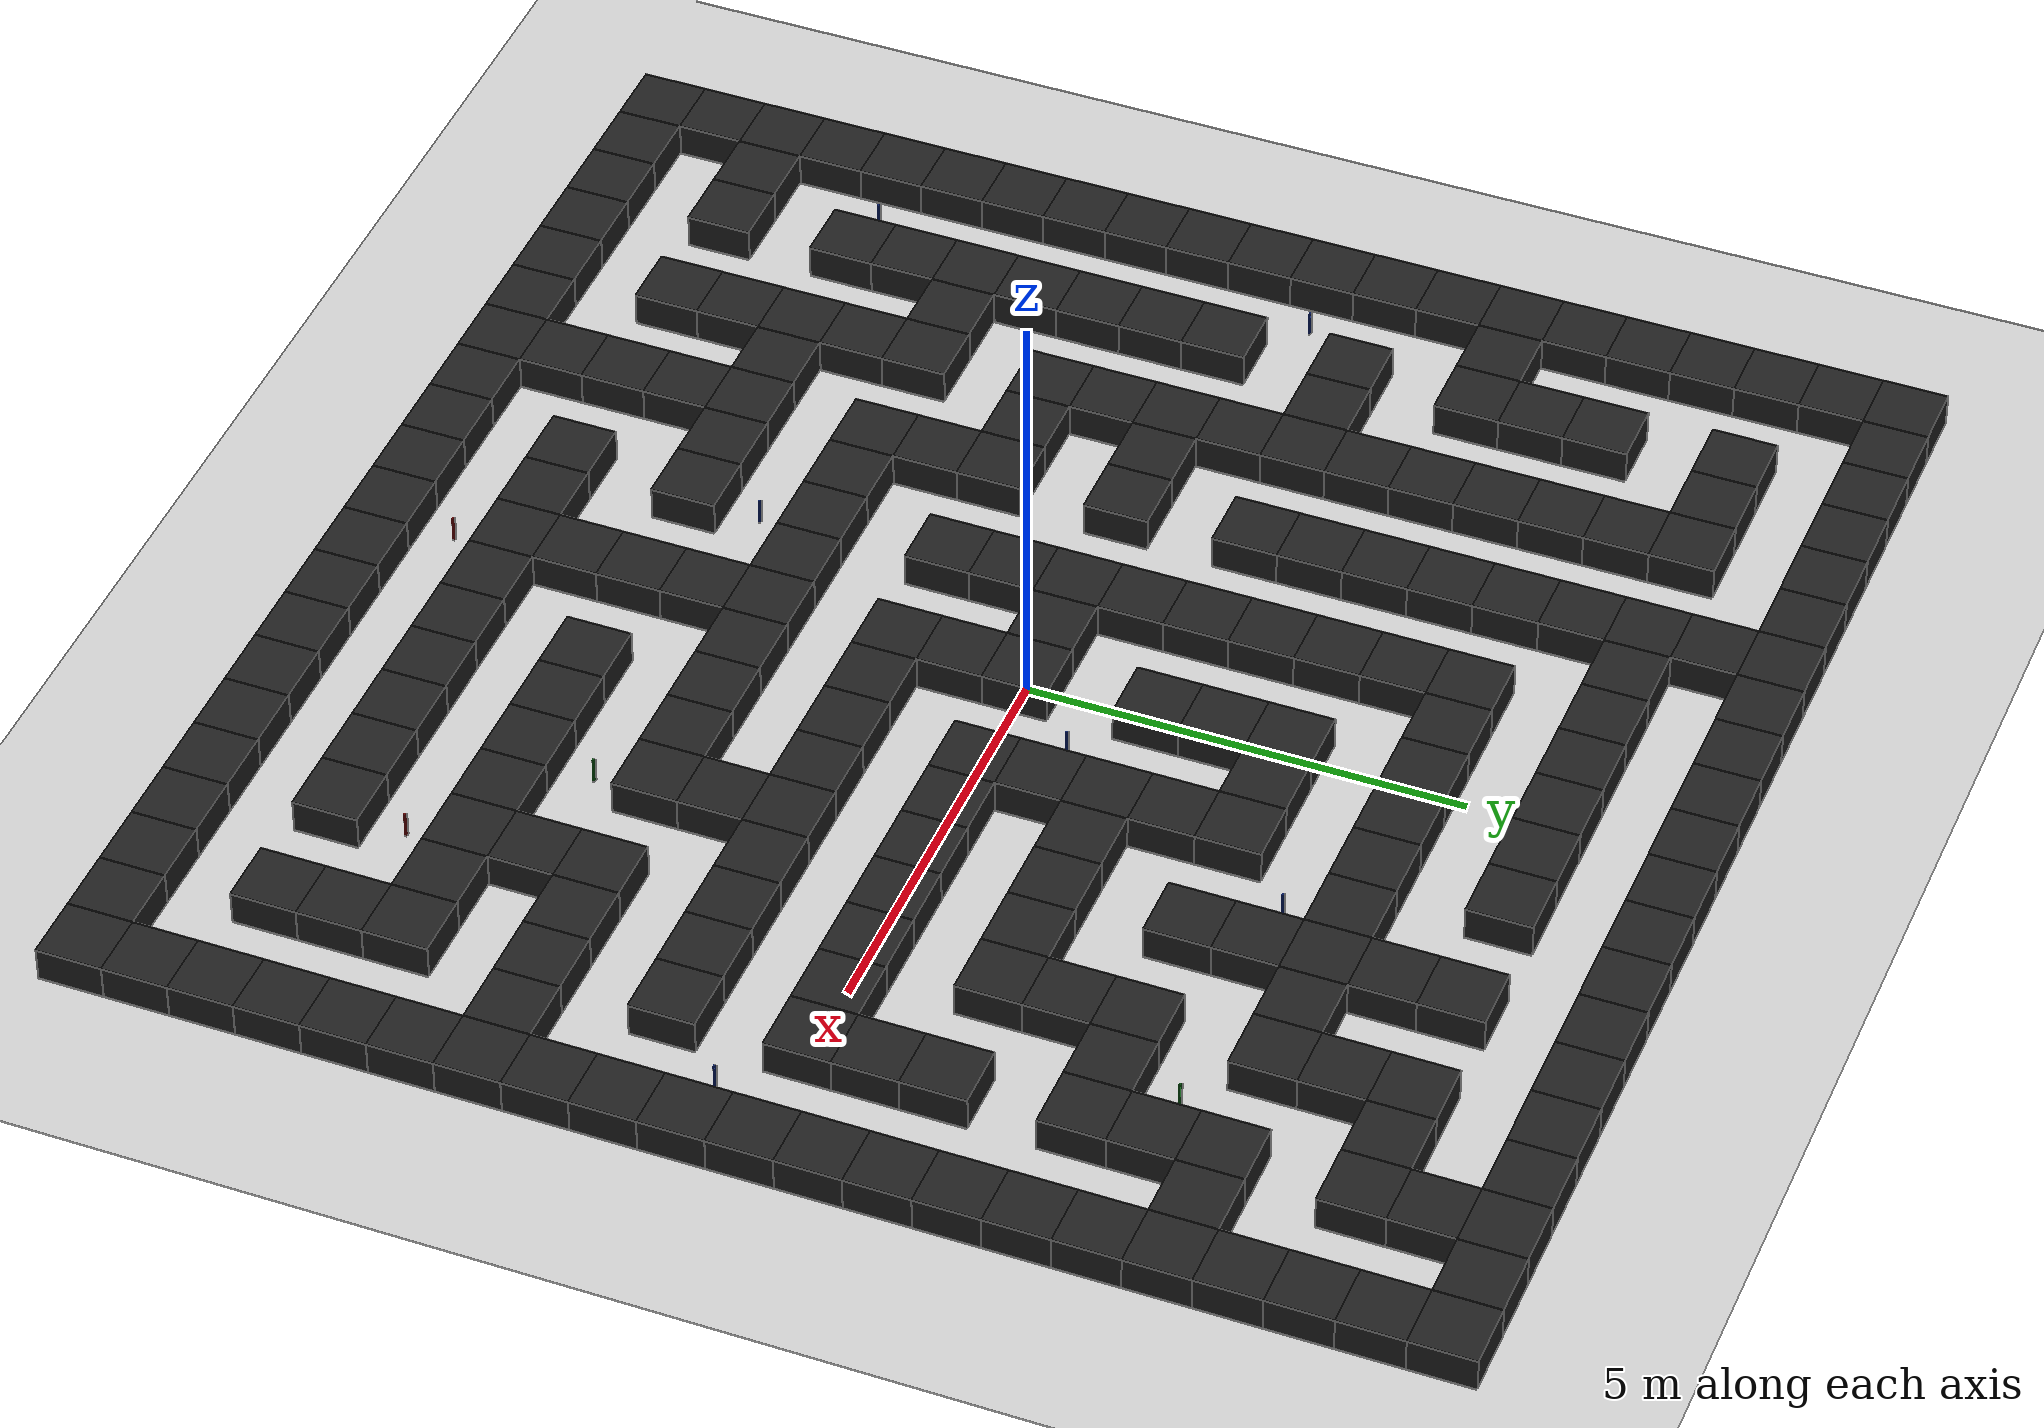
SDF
<?xml version="1.0" ?>
<sdf version="1.6">
  <world name="maze_gems">
    <physics name="1ms" type="ignored">
      <max_step_size>0.001</max_step_size>
      <real_time_factor>1.0</real_time_factor>
    </physics>
    <plugin filename="gz-sim-physics-system" name="gz::sim::systems::Physics"/>
    <plugin filename="gz-sim-user-commands-system" name="gz::sim::systems::UserCommands"/>
    <plugin filename="gz-sim-scene-broadcaster-system" name="gz::sim::systems::SceneBroadcaster"/>
    <plugin filename="gz-sim-sensors-system" name="gz::sim::systems::Sensors">
      <render_engine>ogre2</render_engine>
    </plugin>
    <plugin filename="gz-sim-contact-system" name="gz::sim::systems::Contact"/>
    <plugin filename="gz-sim-imu-system" name="gz::sim::systems::Imu"/>
    <gravity>0 0 -9.81</gravity>
    <magnetic_field>5.5645e-06 2.28758e-05 -4.23884e-05</magnetic_field>
    <include>
      <uri>model://models/sun</uri>
    </include>
    <include>
      <uri>model://models/ground_plane</uri>
    </include>
    <model name="walls">
      <static>true</static>
      <link name="wall_1">
        <pose>7.5 7.5 0.2 0 0 0</pose>
        <visual name="wall_1_visual">
          <geometry>
            <box>
              <size>0.75 0.75 0.4</size>
            </box>
          </geometry>
          <material>
            <script>
              <uri>file://media/materials/scripts/gazebo.material</uri>
              <name>Gazebo/Black</name>
            </script>
          </material>
        </visual>
        <collision name="wall_1_collision">
          <geometry>
            <box>
              <size>0.75 0.75 0.4</size>
            </box>
          </geometry>
        </collision>
      </link>
      <link name="wall_2">
        <pose>7.5 6.75 0.2 0 0 0</pose>
        <visual name="wall_2_visual">
          <geometry>
            <box>
              <size>0.75 0.75 0.4</size>
            </box>
          </geometry>
          <material>
            <script>
              <uri>file://media/materials/scripts/gazebo.material</uri>
              <name>Gazebo/Black</name>
            </script>
          </material>
        </visual>
        <collision name="wall_2_collision">
          <geometry>
            <box>
              <size>0.75 0.75 0.4</size>
            </box>
          </geometry>
        </collision>
      </link>
      <link name="wall_3">
        <pose>7.5 6.0 0.2 0 0 0</pose>
        <visual name="wall_3_visual">
          <geometry>
            <box>
              <size>0.75 0.75 0.4</size>
            </box>
          </geometry>
          <material>
            <script>
              <uri>file://media/materials/scripts/gazebo.material</uri>
              <name>Gazebo/Black</name>
            </script>
          </material>
        </visual>
        <collision name="wall_3_collision">
          <geometry>
            <box>
              <size>0.75 0.75 0.4</size>
            </box>
          </geometry>
        </collision>
      </link>
      <link name="wall_4">
        <pose>7.5 5.25 0.2 0 0 0</pose>
        <visual name="wall_4_visual">
          <geometry>
            <box>
              <size>0.75 0.75 0.4</size>
            </box>
          </geometry>
          <material>
            <script>
              <uri>file://media/materials/scripts/gazebo.material</uri>
              <name>Gazebo/Black</name>
            </script>
          </material>
        </visual>
        <collision name="wall_4_collision">
          <geometry>
            <box>
              <size>0.75 0.75 0.4</size>
            </box>
          </geometry>
        </collision>
      </link>
      <link name="wall_5">
        <pose>7.5 4.5 0.2 0 0 0</pose>
        <visual name="wall_5_visual">
          <geometry>
            <box>
              <size>0.75 0.75 0.4</size>
            </box>
          </geometry>
          <material>
            <script>
              <uri>file://media/materials/scripts/gazebo.material</uri>
              <name>Gazebo/Black</name>
            </script>
          </material>
        </visual>
        <collision name="wall_5_collision">
          <geometry>
            <box>
              <size>0.75 0.75 0.4</size>
            </box>
          </geometry>
        </collision>
      </link>
      <link name="wall_6">
        <pose>7.5 3.75 0.2 0 0 0</pose>
        <visual name="wall_6_visual">
          <geometry>
            <box>
              <size>0.75 0.75 0.4</size>
            </box>
          </geometry>
          <material>
            <script>
              <uri>file://media/materials/scripts/gazebo.material</uri>
              <name>Gazebo/Black</name>
            </script>
          </material>
        </visual>
        <collision name="wall_6_collision">
          <geometry>
            <box>
              <size>0.75 0.75 0.4</size>
            </box>
          </geometry>
        </collision>
      </link>
      <link name="wall_7">
        <pose>7.5 3.0 0.2 0 0 0</pose>
        <visual name="wall_7_visual">
          <geometry>
            <box>
              <size>0.75 0.75 0.4</size>
            </box>
          </geometry>
          <material>
            <script>
              <uri>file://media/materials/scripts/gazebo.material</uri>
              <name>Gazebo/Black</name>
            </script>
          </material>
        </visual>
        <collision name="wall_7_collision">
          <geometry>
            <box>
              <size>0.75 0.75 0.4</size>
            </box>
          </geometry>
        </collision>
      </link>
      <link name="wall_8">
        <pose>7.5 2.25 0.2 0 0 0</pose>
        <visual name="wall_8_visual">
          <geometry>
            <box>
              <size>0.75 0.75 0.4</size>
            </box>
          </geometry>
          <material>
            <script>
              <uri>file://media/materials/scripts/gazebo.material</uri>
              <name>Gazebo/Black</name>
            </script>
          </material>
        </visual>
        <collision name="wall_8_collision">
          <geometry>
            <box>
              <size>0.75 0.75 0.4</size>
            </box>
          </geometry>
        </collision>
      </link>
      <link name="wall_9">
        <pose>7.5 1.5 0.2 0 0 0</pose>
        <visual name="wall_9_visual">
          <geometry>
            <box>
              <size>0.75 0.75 0.4</size>
            </box>
          </geometry>
          <material>
            <script>
              <uri>file://media/materials/scripts/gazebo.material</uri>
              <name>Gazebo/Black</name>
            </script>
          </material>
        </visual>
        <collision name="wall_9_collision">
          <geometry>
            <box>
              <size>0.75 0.75 0.4</size>
            </box>
          </geometry>
        </collision>
      </link>
      <link name="wall_10">
        <pose>7.5 0.75 0.2 0 0 0</pose>
        <visual name="wall_10_visual">
          <geometry>
            <box>
              <size>0.75 0.75 0.4</size>
            </box>
          </geometry>
          <material>
            <script>
              <uri>file://media/materials/scripts/gazebo.material</uri>
              <name>Gazebo/Black</name>
            </script>
          </material>
        </visual>
        <collision name="wall_10_collision">
          <geometry>
            <box>
              <size>0.75 0.75 0.4</size>
            </box>
          </geometry>
        </collision>
      </link>
      <link name="wall_11">
        <pose>7.5 0.0 0.2 0 0 0</pose>
        <visual name="wall_11_visual">
          <geometry>
            <box>
              <size>0.75 0.75 0.4</size>
            </box>
          </geometry>
          <material>
            <script>
              <uri>file://media/materials/scripts/gazebo.material</uri>
              <name>Gazebo/Black</name>
            </script>
          </material>
        </visual>
        <collision name="wall_11_collision">
          <geometry>
            <box>
              <size>0.75 0.75 0.4</size>
            </box>
          </geometry>
        </collision>
      </link>
      <link name="wall_12">
        <pose>7.5 -0.75 0.2 0 0 0</pose>
        <visual name="wall_12_visual">
          <geometry>
            <box>
              <size>0.75 0.75 0.4</size>
            </box>
          </geometry>
          <material>
            <script>
              <uri>file://media/materials/scripts/gazebo.material</uri>
              <name>Gazebo/Black</name>
            </script>
          </material>
        </visual>
        <collision name="wall_12_collision">
          <geometry>
            <box>
              <size>0.75 0.75 0.4</size>
            </box>
          </geometry>
        </collision>
      </link>
      <link name="wall_13">
        <pose>7.5 -1.5 0.2 0 0 0</pose>
        <visual name="wall_13_visual">
          <geometry>
            <box>
              <size>0.75 0.75 0.4</size>
            </box>
          </geometry>
          <material>
            <script>
              <uri>file://media/materials/scripts/gazebo.material</uri>
              <name>Gazebo/Black</name>
            </script>
          </material>
        </visual>
        <collision name="wall_13_collision">
          <geometry>
            <box>
              <size>0.75 0.75 0.4</size>
            </box>
          </geometry>
        </collision>
      </link>
      <link name="wall_14">
        <pose>7.5 -2.25 0.2 0 0 0</pose>
        <visual name="wall_14_visual">
          <geometry>
            <box>
              <size>0.75 0.75 0.4</size>
            </box>
          </geometry>
          <material>
            <script>
              <uri>file://media/materials/scripts/gazebo.material</uri>
              <name>Gazebo/Black</name>
            </script>
          </material>
        </visual>
        <collision name="wall_14_collision">
          <geometry>
            <box>
              <size>0.75 0.75 0.4</size>
            </box>
          </geometry>
        </collision>
      </link>
      <link name="wall_15">
        <pose>7.5 -3.0 0.2 0 0 0</pose>
        <visual name="wall_15_visual">
          <geometry>
            <box>
              <size>0.75 0.75 0.4</size>
            </box>
          </geometry>
          <material>
            <script>
              <uri>file://media/materials/scripts/gazebo.material</uri>
              <name>Gazebo/Black</name>
            </script>
          </material>
        </visual>
        <collision name="wall_15_collision">
          <geometry>
            <box>
              <size>0.75 0.75 0.4</size>
            </box>
          </geometry>
        </collision>
      </link>
      <link name="wall_16">
        <pose>7.5 -3.75 0.2 0 0 0</pose>
        <visual name="wall_16_visual">
          <geometry>
            <box>
              <size>0.75 0.75 0.4</size>
            </box>
          </geometry>
          <material>
            <script>
              <uri>file://media/materials/scripts/gazebo.material</uri>
              <name>Gazebo/Black</name>
            </script>
          </material>
        </visual>
        <collision name="wall_16_collision">
          <geometry>
            <box>
              <size>0.75 0.75 0.4</size>
            </box>
          </geometry>
        </collision>
      </link>
      <link name="wall_17">
        <pose>7.5 -4.5 0.2 0 0 0</pose>
        <visual name="wall_17_visual">
          <geometry>
            <box>
              <size>0.75 0.75 0.4</size>
            </box>
          </geometry>
          <material>
            <script>
              <uri>file://media/materials/scripts/gazebo.material</uri>
              <name>Gazebo/Black</name>
            </script>
          </material>
        </visual>
        <collision name="wall_17_collision">
          <geometry>
            <box>
              <size>0.75 0.75 0.4</size>
            </box>
          </geometry>
        </collision>
      </link>
      <link name="wall_18">
        <pose>7.5 -5.25 0.2 0 0 0</pose>
        <visual name="wall_18_visual">
          <geometry>
            <box>
              <size>0.75 0.75 0.4</size>
            </box>
          </geometry>
          <material>
            <script>
              <uri>file://media/materials/scripts/gazebo.material</uri>
              <name>Gazebo/Black</name>
            </script>
          </material>
        </visual>
        <collision name="wall_18_collision">
          <geometry>
            <box>
              <size>0.75 0.75 0.4</size>
            </box>
          </geometry>
        </collision>
      </link>
      <link name="wall_19">
        <pose>7.5 -6.0 0.2 0 0 0</pose>
        <visual name="wall_19_visual">
          <geometry>
            <box>
              <size>0.75 0.75 0.4</size>
            </box>
          </geometry>
          <material>
            <script>
              <uri>file://media/materials/scripts/gazebo.material</uri>
              <name>Gazebo/Black</name>
            </script>
          </material>
        </visual>
        <collision name="wall_19_collision">
          <geometry>
            <box>
              <size>0.75 0.75 0.4</size>
            </box>
          </geometry>
        </collision>
      </link>
      <link name="wall_20">
        <pose>7.5 -6.75 0.2 0 0 0</pose>
        <visual name="wall_20_visual">
          <geometry>
            <box>
              <size>0.75 0.75 0.4</size>
            </box>
          </geometry>
          <material>
            <script>
              <uri>file://media/materials/scripts/gazebo.material</uri>
              <name>Gazebo/Black</name>
            </script>
          </material>
        </visual>
        <collision name="wall_20_collision">
          <geometry>
            <box>
              <size>0.75 0.75 0.4</size>
            </box>
          </geometry>
        </collision>
      </link>
      <link name="wall_21">
        <pose>7.5 -7.5 0.2 0 0 0</pose>
        <visual name="wall_21_visual">
          <geometry>
            <box>
              <size>0.75 0.75 0.4</size>
            </box>
          </geometry>
          <material>
            <script>
              <uri>file://media/materials/scripts/gazebo.material</uri>
              <name>Gazebo/Black</name>
            </script>
          </material>
        </visual>
        <collision name="wall_21_collision">
          <geometry>
            <box>
              <size>0.75 0.75 0.4</size>
            </box>
          </geometry>
        </collision>
      </link>
      <link name="wall_22">
        <pose>6.75 7.5 0.2 0 0 0</pose>
        <visual name="wall_22_visual">
          <geometry>
            <box>
              <size>0.75 0.75 0.4</size>
            </box>
          </geometry>
          <material>
            <script>
              <uri>file://media/materials/scripts/gazebo.material</uri>
              <name>Gazebo/Black</name>
            </script>
          </material>
        </visual>
        <collision name="wall_22_collision">
          <geometry>
            <box>
              <size>0.75 0.75 0.4</size>
            </box>
          </geometry>
        </collision>
      </link>
      <link name="wall_23">
        <pose>6.75 4.5 0.2 0 0 0</pose>
        <visual name="wall_23_visual">
          <geometry>
            <box>
              <size>0.75 0.75 0.4</size>
            </box>
          </geometry>
          <material>
            <script>
              <uri>file://media/materials/scripts/gazebo.material</uri>
              <name>Gazebo/Black</name>
            </script>
          </material>
        </visual>
        <collision name="wall_23_collision">
          <geometry>
            <box>
              <size>0.75 0.75 0.4</size>
            </box>
          </geometry>
        </collision>
      </link>
      <link name="wall_24">
        <pose>6.75 -3.0 0.2 0 0 0</pose>
        <visual name="wall_24_visual">
          <geometry>
            <box>
              <size>0.75 0.75 0.4</size>
            </box>
          </geometry>
          <material>
            <script>
              <uri>file://media/materials/scripts/gazebo.material</uri>
              <name>Gazebo/Black</name>
            </script>
          </material>
        </visual>
        <collision name="wall_24_collision">
          <geometry>
            <box>
              <size>0.75 0.75 0.4</size>
            </box>
          </geometry>
        </collision>
      </link>
      <link name="wall_25">
        <pose>6.75 -7.5 0.2 0 0 0</pose>
        <visual name="wall_25_visual">
          <geometry>
            <box>
              <size>0.75 0.75 0.4</size>
            </box>
          </geometry>
          <material>
            <script>
              <uri>file://media/materials/scripts/gazebo.material</uri>
              <name>Gazebo/Black</name>
            </script>
          </material>
        </visual>
        <collision name="wall_25_collision">
          <geometry>
            <box>
              <size>0.75 0.75 0.4</size>
            </box>
          </geometry>
        </collision>
      </link>
      <link name="wall_26">
        <pose>6.0 7.5 0.2 0 0 0</pose>
        <visual name="wall_26_visual">
          <geometry>
            <box>
              <size>0.75 0.75 0.4</size>
            </box>
          </geometry>
          <material>
            <script>
              <uri>file://media/materials/scripts/gazebo.material</uri>
              <name>Gazebo/Black</name>
            </script>
          </material>
        </visual>
        <collision name="wall_26_collision">
          <geometry>
            <box>
              <size>0.75 0.75 0.4</size>
            </box>
          </geometry>
        </collision>
      </link>
      <link name="wall_27">
        <pose>6.0 6.75 0.2 0 0 0</pose>
        <visual name="wall_27_visual">
          <geometry>
            <box>
              <size>0.75 0.75 0.4</size>
            </box>
          </geometry>
          <material>
            <script>
              <uri>file://media/materials/scripts/gazebo.material</uri>
              <name>Gazebo/Black</name>
            </script>
          </material>
        </visual>
        <collision name="wall_27_collision">
          <geometry>
            <box>
              <size>0.75 0.75 0.4</size>
            </box>
          </geometry>
        </collision>
      </link>
      <link name="wall_28">
        <pose>6.0 6.0 0.2 0 0 0</pose>
        <visual name="wall_28_visual">
          <geometry>
            <box>
              <size>0.75 0.75 0.4</size>
            </box>
          </geometry>
          <material>
            <script>
              <uri>file://media/materials/scripts/gazebo.material</uri>
              <name>Gazebo/Black</name>
            </script>
          </material>
        </visual>
        <collision name="wall_28_collision">
          <geometry>
            <box>
              <size>0.75 0.75 0.4</size>
            </box>
          </geometry>
        </collision>
      </link>
      <link name="wall_29">
        <pose>6.0 4.5 0.2 0 0 0</pose>
        <visual name="wall_29_visual">
          <geometry>
            <box>
              <size>0.75 0.75 0.4</size>
            </box>
          </geometry>
          <material>
            <script>
              <uri>file://media/materials/scripts/gazebo.material</uri>
              <name>Gazebo/Black</name>
            </script>
          </material>
        </visual>
        <collision name="wall_29_collision">
          <geometry>
            <box>
              <size>0.75 0.75 0.4</size>
            </box>
          </geometry>
        </collision>
      </link>
      <link name="wall_30">
        <pose>6.0 3.75 0.2 0 0 0</pose>
        <visual name="wall_30_visual">
          <geometry>
            <box>
              <size>0.75 0.75 0.4</size>
            </box>
          </geometry>
          <material>
            <script>
              <uri>file://media/materials/scripts/gazebo.material</uri>
              <name>Gazebo/Black</name>
            </script>
          </material>
        </visual>
        <collision name="wall_30_collision">
          <geometry>
            <box>
              <size>0.75 0.75 0.4</size>
            </box>
          </geometry>
        </collision>
      </link>
      <link name="wall_31">
        <pose>6.0 3.0 0.2 0 0 0</pose>
        <visual name="wall_31_visual">
          <geometry>
            <box>
              <size>0.75 0.75 0.4</size>
            </box>
          </geometry>
          <material>
            <script>
              <uri>file://media/materials/scripts/gazebo.material</uri>
              <name>Gazebo/Black</name>
            </script>
          </material>
        </visual>
        <collision name="wall_31_collision">
          <geometry>
            <box>
              <size>0.75 0.75 0.4</size>
            </box>
          </geometry>
        </collision>
      </link>
      <link name="wall_32">
        <pose>6.0 1.5 0.2 0 0 0</pose>
        <visual name="wall_32_visual">
          <geometry>
            <box>
              <size>0.75 0.75 0.4</size>
            </box>
          </geometry>
          <material>
            <script>
              <uri>file://media/materials/scripts/gazebo.material</uri>
              <name>Gazebo/Black</name>
            </script>
          </material>
        </visual>
        <collision name="wall_32_collision">
          <geometry>
            <box>
              <size>0.75 0.75 0.4</size>
            </box>
          </geometry>
        </collision>
      </link>
      <link name="wall_33">
        <pose>6.0 0.75 0.2 0 0 0</pose>
        <visual name="wall_33_visual">
          <geometry>
            <box>
              <size>0.75 0.75 0.4</size>
            </box>
          </geometry>
          <material>
            <script>
              <uri>file://media/materials/scripts/gazebo.material</uri>
              <name>Gazebo/Black</name>
            </script>
          </material>
        </visual>
        <collision name="wall_33_collision">
          <geometry>
            <box>
              <size>0.75 0.75 0.4</size>
            </box>
          </geometry>
        </collision>
      </link>
      <link name="wall_34">
        <pose>6.0 0.0 0.2 0 0 0</pose>
        <visual name="wall_34_visual">
          <geometry>
            <box>
              <size>0.75 0.75 0.4</size>
            </box>
          </geometry>
          <material>
            <script>
              <uri>file://media/materials/scripts/gazebo.material</uri>
              <name>Gazebo/Black</name>
            </script>
          </material>
        </visual>
        <collision name="wall_34_collision">
          <geometry>
            <box>
              <size>0.75 0.75 0.4</size>
            </box>
          </geometry>
        </collision>
      </link>
      <link name="wall_35">
        <pose>6.0 -1.5 0.2 0 0 0</pose>
        <visual name="wall_35_visual">
          <geometry>
            <box>
              <size>0.75 0.75 0.4</size>
            </box>
          </geometry>
          <material>
            <script>
              <uri>file://media/materials/scripts/gazebo.material</uri>
              <name>Gazebo/Black</name>
            </script>
          </material>
        </visual>
        <collision name="wall_35_collision">
          <geometry>
            <box>
              <size>0.75 0.75 0.4</size>
            </box>
          </geometry>
        </collision>
      </link>
      <link name="wall_36">
        <pose>6.0 -3.0 0.2 0 0 0</pose>
        <visual name="wall_36_visual">
          <geometry>
            <box>
              <size>0.75 0.75 0.4</size>
            </box>
          </geometry>
          <material>
            <script>
              <uri>file://media/materials/scripts/gazebo.material</uri>
              <name>Gazebo/Black</name>
            </script>
          </material>
        </visual>
        <collision name="wall_36_collision">
          <geometry>
            <box>
              <size>0.75 0.75 0.4</size>
            </box>
          </geometry>
        </collision>
      </link>
      <link name="wall_37">
        <pose>6.0 -4.5 0.2 0 0 0</pose>
        <visual name="wall_37_visual">
          <geometry>
            <box>
              <size>0.75 0.75 0.4</size>
            </box>
          </geometry>
          <material>
            <script>
              <uri>file://media/materials/scripts/gazebo.material</uri>
              <name>Gazebo/Black</name>
            </script>
          </material>
        </visual>
        <collision name="wall_37_collision">
          <geometry>
            <box>
              <size>0.75 0.75 0.4</size>
            </box>
          </geometry>
        </collision>
      </link>
      <link name="wall_38">
        <pose>6.0 -5.25 0.2 0 0 0</pose>
        <visual name="wall_38_visual">
          <geometry>
            <box>
              <size>0.75 0.75 0.4</size>
            </box>
          </geometry>
          <material>
            <script>
              <uri>file://media/materials/scripts/gazebo.material</uri>
              <name>Gazebo/Black</name>
            </script>
          </material>
        </visual>
        <collision name="wall_38_collision">
          <geometry>
            <box>
              <size>0.75 0.75 0.4</size>
            </box>
          </geometry>
        </collision>
      </link>
      <link name="wall_39">
        <pose>6.0 -6.0 0.2 0 0 0</pose>
        <visual name="wall_39_visual">
          <geometry>
            <box>
              <size>0.75 0.75 0.4</size>
            </box>
          </geometry>
          <material>
            <script>
              <uri>file://media/materials/scripts/gazebo.material</uri>
              <name>Gazebo/Black</name>
            </script>
          </material>
        </visual>
        <collision name="wall_39_collision">
          <geometry>
            <box>
              <size>0.75 0.75 0.4</size>
            </box>
          </geometry>
        </collision>
      </link>
      <link name="wall_40">
        <pose>6.0 -7.5 0.2 0 0 0</pose>
        <visual name="wall_40_visual">
          <geometry>
            <box>
              <size>0.75 0.75 0.4</size>
            </box>
          </geometry>
          <material>
            <script>
              <uri>file://media/materials/scripts/gazebo.material</uri>
              <name>Gazebo/Black</name>
            </script>
          </material>
        </visual>
        <collision name="wall_40_collision">
          <geometry>
            <box>
              <size>0.75 0.75 0.4</size>
            </box>
          </geometry>
        </collision>
      </link>
      <link name="wall_41">
        <pose>5.25 7.5 0.2 0 0 0</pose>
        <visual name="wall_41_visual">
          <geometry>
            <box>
              <size>0.75 0.75 0.4</size>
            </box>
          </geometry>
          <material>
            <script>
              <uri>file://media/materials/scripts/gazebo.material</uri>
              <name>Gazebo/Black</name>
            </script>
          </material>
        </visual>
        <collision name="wall_41_collision">
          <geometry>
            <box>
              <size>0.75 0.75 0.4</size>
            </box>
          </geometry>
        </collision>
      </link>
      <link name="wall_42">
        <pose>5.25 6.0 0.2 0 0 0</pose>
        <visual name="wall_42_visual">
          <geometry>
            <box>
              <size>0.75 0.75 0.4</size>
            </box>
          </geometry>
          <material>
            <script>
              <uri>file://media/materials/scripts/gazebo.material</uri>
              <name>Gazebo/Black</name>
            </script>
          </material>
        </visual>
        <collision name="wall_42_collision">
          <geometry>
            <box>
              <size>0.75 0.75 0.4</size>
            </box>
          </geometry>
        </collision>
      </link>
      <link name="wall_43">
        <pose>5.25 3.0 0.2 0 0 0</pose>
        <visual name="wall_43_visual">
          <geometry>
            <box>
              <size>0.75 0.75 0.4</size>
            </box>
          </geometry>
          <material>
            <script>
              <uri>file://media/materials/scripts/gazebo.material</uri>
              <name>Gazebo/Black</name>
            </script>
          </material>
        </visual>
        <collision name="wall_43_collision">
          <geometry>
            <box>
              <size>0.75 0.75 0.4</size>
            </box>
          </geometry>
        </collision>
      </link>
      <link name="wall_44">
        <pose>5.25 0.0 0.2 0 0 0</pose>
        <visual name="wall_44_visual">
          <geometry>
            <box>
              <size>0.75 0.75 0.4</size>
            </box>
          </geometry>
          <material>
            <script>
              <uri>file://media/materials/scripts/gazebo.material</uri>
              <name>Gazebo/Black</name>
            </script>
          </material>
        </visual>
        <collision name="wall_44_collision">
          <geometry>
            <box>
              <size>0.75 0.75 0.4</size>
            </box>
          </geometry>
        </collision>
      </link>
      <link name="wall_45">
        <pose>5.25 -1.5 0.2 0 0 0</pose>
        <visual name="wall_45_visual">
          <geometry>
            <box>
              <size>0.75 0.75 0.4</size>
            </box>
          </geometry>
          <material>
            <script>
              <uri>file://media/materials/scripts/gazebo.material</uri>
              <name>Gazebo/Black</name>
            </script>
          </material>
        </visual>
        <collision name="wall_45_collision">
          <geometry>
            <box>
              <size>0.75 0.75 0.4</size>
            </box>
          </geometry>
        </collision>
      </link>
      <link name="wall_46">
        <pose>5.25 -3.0 0.2 0 0 0</pose>
        <visual name="wall_46_visual">
          <geometry>
            <box>
              <size>0.75 0.75 0.4</size>
            </box>
          </geometry>
          <material>
            <script>
              <uri>file://media/materials/scripts/gazebo.material</uri>
              <name>Gazebo/Black</name>
            </script>
          </material>
        </visual>
        <collision name="wall_46_collision">
          <geometry>
            <box>
              <size>0.75 0.75 0.4</size>
            </box>
          </geometry>
        </collision>
      </link>
      <link name="wall_47">
        <pose>5.25 -4.5 0.2 0 0 0</pose>
        <visual name="wall_47_visual">
          <geometry>
            <box>
              <size>0.75 0.75 0.4</size>
            </box>
          </geometry>
          <material>
            <script>
              <uri>file://media/materials/scripts/gazebo.material</uri>
              <name>Gazebo/Black</name>
            </script>
          </material>
        </visual>
        <collision name="wall_47_collision">
          <geometry>
            <box>
              <size>0.75 0.75 0.4</size>
            </box>
          </geometry>
        </collision>
      </link>
      <link name="wall_48">
        <pose>5.25 -7.5 0.2 0 0 0</pose>
        <visual name="wall_48_visual">
          <geometry>
            <box>
              <size>0.75 0.75 0.4</size>
            </box>
          </geometry>
          <material>
            <script>
              <uri>file://media/materials/scripts/gazebo.material</uri>
              <name>Gazebo/Black</name>
            </script>
          </material>
        </visual>
        <collision name="wall_48_collision">
          <geometry>
            <box>
              <size>0.75 0.75 0.4</size>
            </box>
          </geometry>
        </collision>
      </link>
      <link name="wall_49">
        <pose>4.5 7.5 0.2 0 0 0</pose>
        <visual name="wall_49_visual">
          <geometry>
            <box>
              <size>0.75 0.75 0.4</size>
            </box>
          </geometry>
          <material>
            <script>
              <uri>file://media/materials/scripts/gazebo.material</uri>
              <name>Gazebo/Black</name>
            </script>
          </material>
        </visual>
        <collision name="wall_49_collision">
          <geometry>
            <box>
              <size>0.75 0.75 0.4</size>
            </box>
          </geometry>
        </collision>
      </link>
      <link name="wall_50">
        <pose>4.5 6.0 0.2 0 0 0</pose>
        <visual name="wall_50_visual">
          <geometry>
            <box>
              <size>0.75 0.75 0.4</size>
            </box>
          </geometry>
          <material>
            <script>
              <uri>file://media/materials/scripts/gazebo.material</uri>
              <name>Gazebo/Black</name>
            </script>
          </material>
        </visual>
        <collision name="wall_50_collision">
          <geometry>
            <box>
              <size>0.75 0.75 0.4</size>
            </box>
          </geometry>
        </collision>
      </link>
      <link name="wall_51">
        <pose>4.5 5.25 0.2 0 0 0</pose>
        <visual name="wall_51_visual">
          <geometry>
            <box>
              <size>0.75 0.75 0.4</size>
            </box>
          </geometry>
          <material>
            <script>
              <uri>file://media/materials/scripts/gazebo.material</uri>
              <name>Gazebo/Black</name>
            </script>
          </material>
        </visual>
        <collision name="wall_51_collision">
          <geometry>
            <box>
              <size>0.75 0.75 0.4</size>
            </box>
          </geometry>
        </collision>
      </link>
      <link name="wall_52">
        <pose>4.5 4.5 0.2 0 0 0</pose>
        <visual name="wall_52_visual">
          <geometry>
            <box>
              <size>0.75 0.75 0.4</size>
            </box>
          </geometry>
          <material>
            <script>
              <uri>file://media/materials/scripts/gazebo.material</uri>
              <name>Gazebo/Black</name>
            </script>
          </material>
        </visual>
        <collision name="wall_52_collision">
          <geometry>
            <box>
              <size>0.75 0.75 0.4</size>
            </box>
          </geometry>
        </collision>
      </link>
      <link name="wall_53">
        <pose>4.5 3.0 0.2 0 0 0</pose>
        <visual name="wall_53_visual">
          <geometry>
            <box>
              <size>0.75 0.75 0.4</size>
            </box>
          </geometry>
          <material>
            <script>
              <uri>file://media/materials/scripts/gazebo.material</uri>
              <name>Gazebo/Black</name>
            </script>
          </material>
        </visual>
        <collision name="wall_53_collision">
          <geometry>
            <box>
              <size>0.75 0.75 0.4</size>
            </box>
          </geometry>
        </collision>
      </link>
      <link name="wall_54">
        <pose>4.5 2.25 0.2 0 0 0</pose>
        <visual name="wall_54_visual">
          <geometry>
            <box>
              <size>0.75 0.75 0.4</size>
            </box>
          </geometry>
          <material>
            <script>
              <uri>file://media/materials/scripts/gazebo.material</uri>
              <name>Gazebo/Black</name>
            </script>
          </material>
        </visual>
        <collision name="wall_54_collision">
          <geometry>
            <box>
              <size>0.75 0.75 0.4</size>
            </box>
          </geometry>
        </collision>
      </link>
      <link name="wall_55">
        <pose>4.5 1.5 0.2 0 0 0</pose>
        <visual name="wall_55_visual">
          <geometry>
            <box>
              <size>0.75 0.75 0.4</size>
            </box>
          </geometry>
          <material>
            <script>
              <uri>file://media/materials/scripts/gazebo.material</uri>
              <name>Gazebo/Black</name>
            </script>
          </material>
        </visual>
        <collision name="wall_55_collision">
          <geometry>
            <box>
              <size>0.75 0.75 0.4</size>
            </box>
          </geometry>
        </collision>
      </link>
      <link name="wall_56">
        <pose>4.5 0.0 0.2 0 0 0</pose>
        <visual name="wall_56_visual">
          <geometry>
            <box>
              <size>0.75 0.75 0.4</size>
            </box>
          </geometry>
          <material>
            <script>
              <uri>file://media/materials/scripts/gazebo.material</uri>
              <name>Gazebo/Black</name>
            </script>
          </material>
        </visual>
        <collision name="wall_56_collision">
          <geometry>
            <box>
              <size>0.75 0.75 0.4</size>
            </box>
          </geometry>
        </collision>
      </link>
      <link name="wall_57">
        <pose>4.5 -1.5 0.2 0 0 0</pose>
        <visual name="wall_57_visual">
          <geometry>
            <box>
              <size>0.75 0.75 0.4</size>
            </box>
          </geometry>
          <material>
            <script>
              <uri>file://media/materials/scripts/gazebo.material</uri>
              <name>Gazebo/Black</name>
            </script>
          </material>
        </visual>
        <collision name="wall_57_collision">
          <geometry>
            <box>
              <size>0.75 0.75 0.4</size>
            </box>
          </geometry>
        </collision>
      </link>
      <link name="wall_58">
        <pose>4.5 -3.0 0.2 0 0 0</pose>
        <visual name="wall_58_visual">
          <geometry>
            <box>
              <size>0.75 0.75 0.4</size>
            </box>
          </geometry>
          <material>
            <script>
              <uri>file://media/materials/scripts/gazebo.material</uri>
              <name>Gazebo/Black</name>
            </script>
          </material>
        </visual>
        <collision name="wall_58_collision">
          <geometry>
            <box>
              <size>0.75 0.75 0.4</size>
            </box>
          </geometry>
        </collision>
      </link>
      <link name="wall_59">
        <pose>4.5 -3.75 0.2 0 0 0</pose>
        <visual name="wall_59_visual">
          <geometry>
            <box>
              <size>0.75 0.75 0.4</size>
            </box>
          </geometry>
          <material>
            <script>
              <uri>file://media/materials/scripts/gazebo.material</uri>
              <name>Gazebo/Black</name>
            </script>
          </material>
        </visual>
        <collision name="wall_59_collision">
          <geometry>
            <box>
              <size>0.75 0.75 0.4</size>
            </box>
          </geometry>
        </collision>
      </link>
      <link name="wall_60">
        <pose>4.5 -4.5 0.2 0 0 0</pose>
        <visual name="wall_60_visual">
          <geometry>
            <box>
              <size>0.75 0.75 0.4</size>
            </box>
          </geometry>
          <material>
            <script>
              <uri>file://media/materials/scripts/gazebo.material</uri>
              <name>Gazebo/Black</name>
            </script>
          </material>
        </visual>
        <collision name="wall_60_collision">
          <geometry>
            <box>
              <size>0.75 0.75 0.4</size>
            </box>
          </geometry>
        </collision>
      </link>
      <link name="wall_61">
        <pose>4.5 -6.0 0.2 0 0 0</pose>
        <visual name="wall_61_visual">
          <geometry>
            <box>
              <size>0.75 0.75 0.4</size>
            </box>
          </geometry>
          <material>
            <script>
              <uri>file://media/materials/scripts/gazebo.material</uri>
              <name>Gazebo/Black</name>
            </script>
          </material>
        </visual>
        <collision name="wall_61_collision">
          <geometry>
            <box>
              <size>0.75 0.75 0.4</size>
            </box>
          </geometry>
        </collision>
      </link>
      <link name="wall_62">
        <pose>4.5 -7.5 0.2 0 0 0</pose>
        <visual name="wall_62_visual">
          <geometry>
            <box>
              <size>0.75 0.75 0.4</size>
            </box>
          </geometry>
          <material>
            <script>
              <uri>file://media/materials/scripts/gazebo.material</uri>
              <name>Gazebo/Black</name>
            </script>
          </material>
        </visual>
        <collision name="wall_62_collision">
          <geometry>
            <box>
              <size>0.75 0.75 0.4</size>
            </box>
          </geometry>
        </collision>
      </link>
      <link name="wall_63">
        <pose>3.75 7.5 0.2 0 0 0</pose>
        <visual name="wall_63_visual">
          <geometry>
            <box>
              <size>0.75 0.75 0.4</size>
            </box>
          </geometry>
          <material>
            <script>
              <uri>file://media/materials/scripts/gazebo.material</uri>
              <name>Gazebo/Black</name>
            </script>
          </material>
        </visual>
        <collision name="wall_63_collision">
          <geometry>
            <box>
              <size>0.75 0.75 0.4</size>
            </box>
          </geometry>
        </collision>
      </link>
      <link name="wall_64">
        <pose>3.75 4.5 0.2 0 0 0</pose>
        <visual name="wall_64_visual">
          <geometry>
            <box>
              <size>0.75 0.75 0.4</size>
            </box>
          </geometry>
          <material>
            <script>
              <uri>file://media/materials/scripts/gazebo.material</uri>
              <name>Gazebo/Black</name>
            </script>
          </material>
        </visual>
        <collision name="wall_64_collision">
          <geometry>
            <box>
              <size>0.75 0.75 0.4</size>
            </box>
          </geometry>
        </collision>
      </link>
      <link name="wall_65">
        <pose>3.75 1.5 0.2 0 0 0</pose>
        <visual name="wall_65_visual">
          <geometry>
            <box>
              <size>0.75 0.75 0.4</size>
            </box>
          </geometry>
          <material>
            <script>
              <uri>file://media/materials/scripts/gazebo.material</uri>
              <name>Gazebo/Black</name>
            </script>
          </material>
        </visual>
        <collision name="wall_65_collision">
          <geometry>
            <box>
              <size>0.75 0.75 0.4</size>
            </box>
          </geometry>
        </collision>
      </link>
      <link name="wall_66">
        <pose>3.75 0.0 0.2 0 0 0</pose>
        <visual name="wall_66_visual">
          <geometry>
            <box>
              <size>0.75 0.75 0.4</size>
            </box>
          </geometry>
          <material>
            <script>
              <uri>file://media/materials/scripts/gazebo.material</uri>
              <name>Gazebo/Black</name>
            </script>
          </material>
        </visual>
        <collision name="wall_66_collision">
          <geometry>
            <box>
              <size>0.75 0.75 0.4</size>
            </box>
          </geometry>
        </collision>
      </link>
      <link name="wall_67">
        <pose>3.75 -1.5 0.2 0 0 0</pose>
        <visual name="wall_67_visual">
          <geometry>
            <box>
              <size>0.75 0.75 0.4</size>
            </box>
          </geometry>
          <material>
            <script>
              <uri>file://media/materials/scripts/gazebo.material</uri>
              <name>Gazebo/Black</name>
            </script>
          </material>
        </visual>
        <collision name="wall_67_collision">
          <geometry>
            <box>
              <size>0.75 0.75 0.4</size>
            </box>
          </geometry>
        </collision>
      </link>
      <link name="wall_68">
        <pose>3.75 -4.5 0.2 0 0 0</pose>
        <visual name="wall_68_visual">
          <geometry>
            <box>
              <size>0.75 0.75 0.4</size>
            </box>
          </geometry>
          <material>
            <script>
              <uri>file://media/materials/scripts/gazebo.material</uri>
              <name>Gazebo/Black</name>
            </script>
          </material>
        </visual>
        <collision name="wall_68_collision">
          <geometry>
            <box>
              <size>0.75 0.75 0.4</size>
            </box>
          </geometry>
        </collision>
      </link>
      <link name="wall_69">
        <pose>3.75 -6.0 0.2 0 0 0</pose>
        <visual name="wall_69_visual">
          <geometry>
            <box>
              <size>0.75 0.75 0.4</size>
            </box>
          </geometry>
          <material>
            <script>
              <uri>file://media/materials/scripts/gazebo.material</uri>
              <name>Gazebo/Black</name>
            </script>
          </material>
        </visual>
        <collision name="wall_69_collision">
          <geometry>
            <box>
              <size>0.75 0.75 0.4</size>
            </box>
          </geometry>
        </collision>
      </link>
      <link name="wall_70">
        <pose>3.75 -7.5 0.2 0 0 0</pose>
        <visual name="wall_70_visual">
          <geometry>
            <box>
              <size>0.75 0.75 0.4</size>
            </box>
          </geometry>
          <material>
            <script>
              <uri>file://media/materials/scripts/gazebo.material</uri>
              <name>Gazebo/Black</name>
            </script>
          </material>
        </visual>
        <collision name="wall_70_collision">
          <geometry>
            <box>
              <size>0.75 0.75 0.4</size>
            </box>
          </geometry>
        </collision>
      </link>
      <link name="wall_71">
        <pose>3.0 7.5 0.2 0 0 0</pose>
        <visual name="wall_71_visual">
          <geometry>
            <box>
              <size>0.75 0.75 0.4</size>
            </box>
          </geometry>
          <material>
            <script>
              <uri>file://media/materials/scripts/gazebo.material</uri>
              <name>Gazebo/Black</name>
            </script>
          </material>
        </visual>
        <collision name="wall_71_collision">
          <geometry>
            <box>
              <size>0.75 0.75 0.4</size>
            </box>
          </geometry>
        </collision>
      </link>
      <link name="wall_72">
        <pose>3.0 6.0 0.2 0 0 0</pose>
        <visual name="wall_72_visual">
          <geometry>
            <box>
              <size>0.75 0.75 0.4</size>
            </box>
          </geometry>
          <material>
            <script>
              <uri>file://media/materials/scripts/gazebo.material</uri>
              <name>Gazebo/Black</name>
            </script>
          </material>
        </visual>
        <collision name="wall_72_collision">
          <geometry>
            <box>
              <size>0.75 0.75 0.4</size>
            </box>
          </geometry>
        </collision>
      </link>
      <link name="wall_73">
        <pose>3.0 5.25 0.2 0 0 0</pose>
        <visual name="wall_73_visual">
          <geometry>
            <box>
              <size>0.75 0.75 0.4</size>
            </box>
          </geometry>
          <material>
            <script>
              <uri>file://media/materials/scripts/gazebo.material</uri>
              <name>Gazebo/Black</name>
            </script>
          </material>
        </visual>
        <collision name="wall_73_collision">
          <geometry>
            <box>
              <size>0.75 0.75 0.4</size>
            </box>
          </geometry>
        </collision>
      </link>
      <link name="wall_74">
        <pose>3.0 4.5 0.2 0 0 0</pose>
        <visual name="wall_74_visual">
          <geometry>
            <box>
              <size>0.75 0.75 0.4</size>
            </box>
          </geometry>
          <material>
            <script>
              <uri>file://media/materials/scripts/gazebo.material</uri>
              <name>Gazebo/Black</name>
            </script>
          </material>
        </visual>
        <collision name="wall_74_collision">
          <geometry>
            <box>
              <size>0.75 0.75 0.4</size>
            </box>
          </geometry>
        </collision>
      </link>
      <link name="wall_75">
        <pose>3.0 3.75 0.2 0 0 0</pose>
        <visual name="wall_75_visual">
          <geometry>
            <box>
              <size>0.75 0.75 0.4</size>
            </box>
          </geometry>
          <material>
            <script>
              <uri>file://media/materials/scripts/gazebo.material</uri>
              <name>Gazebo/Black</name>
            </script>
          </material>
        </visual>
        <collision name="wall_75_collision">
          <geometry>
            <box>
              <size>0.75 0.75 0.4</size>
            </box>
          </geometry>
        </collision>
      </link>
      <link name="wall_76">
        <pose>3.0 3.0 0.2 0 0 0</pose>
        <visual name="wall_76_visual">
          <geometry>
            <box>
              <size>0.75 0.75 0.4</size>
            </box>
          </geometry>
          <material>
            <script>
              <uri>file://media/materials/scripts/gazebo.material</uri>
              <name>Gazebo/Black</name>
            </script>
          </material>
        </visual>
        <collision name="wall_76_collision">
          <geometry>
            <box>
              <size>0.75 0.75 0.4</size>
            </box>
          </geometry>
        </collision>
      </link>
      <link name="wall_77">
        <pose>3.0 1.5 0.2 0 0 0</pose>
        <visual name="wall_77_visual">
          <geometry>
            <box>
              <size>0.75 0.75 0.4</size>
            </box>
          </geometry>
          <material>
            <script>
              <uri>file://media/materials/scripts/gazebo.material</uri>
              <name>Gazebo/Black</name>
            </script>
          </material>
        </visual>
        <collision name="wall_77_collision">
          <geometry>
            <box>
              <size>0.75 0.75 0.4</size>
            </box>
          </geometry>
        </collision>
      </link>
      <link name="wall_78">
        <pose>3.0 0.0 0.2 0 0 0</pose>
        <visual name="wall_78_visual">
          <geometry>
            <box>
              <size>0.75 0.75 0.4</size>
            </box>
          </geometry>
          <material>
            <script>
              <uri>file://media/materials/scripts/gazebo.material</uri>
              <name>Gazebo/Black</name>
            </script>
          </material>
        </visual>
        <collision name="wall_78_collision">
          <geometry>
            <box>
              <size>0.75 0.75 0.4</size>
            </box>
          </geometry>
        </collision>
      </link>
      <link name="wall_79">
        <pose>3.0 -1.5 0.2 0 0 0</pose>
        <visual name="wall_79_visual">
          <geometry>
            <box>
              <size>0.75 0.75 0.4</size>
            </box>
          </geometry>
          <material>
            <script>
              <uri>file://media/materials/scripts/gazebo.material</uri>
              <name>Gazebo/Black</name>
            </script>
          </material>
        </visual>
        <collision name="wall_79_collision">
          <geometry>
            <box>
              <size>0.75 0.75 0.4</size>
            </box>
          </geometry>
        </collision>
      </link>
      <link name="wall_80">
        <pose>3.0 -2.25 0.2 0 0 0</pose>
        <visual name="wall_80_visual">
          <geometry>
            <box>
              <size>0.75 0.75 0.4</size>
            </box>
          </geometry>
          <material>
            <script>
              <uri>file://media/materials/scripts/gazebo.material</uri>
              <name>Gazebo/Black</name>
            </script>
          </material>
        </visual>
        <collision name="wall_80_collision">
          <geometry>
            <box>
              <size>0.75 0.75 0.4</size>
            </box>
          </geometry>
        </collision>
      </link>
      <link name="wall_81">
        <pose>3.0 -3.0 0.2 0 0 0</pose>
        <visual name="wall_81_visual">
          <geometry>
            <box>
              <size>0.75 0.75 0.4</size>
            </box>
          </geometry>
          <material>
            <script>
              <uri>file://media/materials/scripts/gazebo.material</uri>
              <name>Gazebo/Black</name>
            </script>
          </material>
        </visual>
        <collision name="wall_81_collision">
          <geometry>
            <box>
              <size>0.75 0.75 0.4</size>
            </box>
          </geometry>
        </collision>
      </link>
      <link name="wall_82">
        <pose>3.0 -4.5 0.2 0 0 0</pose>
        <visual name="wall_82_visual">
          <geometry>
            <box>
              <size>0.75 0.75 0.4</size>
            </box>
          </geometry>
          <material>
            <script>
              <uri>file://media/materials/scripts/gazebo.material</uri>
              <name>Gazebo/Black</name>
            </script>
          </material>
        </visual>
        <collision name="wall_82_collision">
          <geometry>
            <box>
              <size>0.75 0.75 0.4</size>
            </box>
          </geometry>
        </collision>
      </link>
      <link name="wall_83">
        <pose>3.0 -6.0 0.2 0 0 0</pose>
        <visual name="wall_83_visual">
          <geometry>
            <box>
              <size>0.75 0.75 0.4</size>
            </box>
          </geometry>
          <material>
            <script>
              <uri>file://media/materials/scripts/gazebo.material</uri>
              <name>Gazebo/Black</name>
            </script>
          </material>
        </visual>
        <collision name="wall_83_collision">
          <geometry>
            <box>
              <size>0.75 0.75 0.4</size>
            </box>
          </geometry>
        </collision>
      </link>
      <link name="wall_84">
        <pose>3.0 -7.5 0.2 0 0 0</pose>
        <visual name="wall_84_visual">
          <geometry>
            <box>
              <size>0.75 0.75 0.4</size>
            </box>
          </geometry>
          <material>
            <script>
              <uri>file://media/materials/scripts/gazebo.material</uri>
              <name>Gazebo/Black</name>
            </script>
          </material>
        </visual>
        <collision name="wall_84_collision">
          <geometry>
            <box>
              <size>0.75 0.75 0.4</size>
            </box>
          </geometry>
        </collision>
      </link>
      <link name="wall_85">
        <pose>2.25 7.5 0.2 0 0 0</pose>
        <visual name="wall_85_visual">
          <geometry>
            <box>
              <size>0.75 0.75 0.4</size>
            </box>
          </geometry>
          <material>
            <script>
              <uri>file://media/materials/scripts/gazebo.material</uri>
              <name>Gazebo/Black</name>
            </script>
          </material>
        </visual>
        <collision name="wall_85_collision">
          <geometry>
            <box>
              <size>0.75 0.75 0.4</size>
            </box>
          </geometry>
        </collision>
      </link>
      <link name="wall_86">
        <pose>2.25 4.5 0.2 0 0 0</pose>
        <visual name="wall_86_visual">
          <geometry>
            <box>
              <size>0.75 0.75 0.4</size>
            </box>
          </geometry>
          <material>
            <script>
              <uri>file://media/materials/scripts/gazebo.material</uri>
              <name>Gazebo/Black</name>
            </script>
          </material>
        </visual>
        <collision name="wall_86_collision">
          <geometry>
            <box>
              <size>0.75 0.75 0.4</size>
            </box>
          </geometry>
        </collision>
      </link>
      <link name="wall_87">
        <pose>2.25 1.5 0.2 0 0 0</pose>
        <visual name="wall_87_visual">
          <geometry>
            <box>
              <size>0.75 0.75 0.4</size>
            </box>
          </geometry>
          <material>
            <script>
              <uri>file://media/materials/scripts/gazebo.material</uri>
              <name>Gazebo/Black</name>
            </script>
          </material>
        </visual>
        <collision name="wall_87_collision">
          <geometry>
            <box>
              <size>0.75 0.75 0.4</size>
            </box>
          </geometry>
        </collision>
      </link>
      <link name="wall_88">
        <pose>2.25 0.0 0.2 0 0 0</pose>
        <visual name="wall_88_visual">
          <geometry>
            <box>
              <size>0.75 0.75 0.4</size>
            </box>
          </geometry>
          <material>
            <script>
              <uri>file://media/materials/scripts/gazebo.material</uri>
              <name>Gazebo/Black</name>
            </script>
          </material>
        </visual>
        <collision name="wall_88_collision">
          <geometry>
            <box>
              <size>0.75 0.75 0.4</size>
            </box>
          </geometry>
        </collision>
      </link>
      <link name="wall_89">
        <pose>2.25 -1.5 0.2 0 0 0</pose>
        <visual name="wall_89_visual">
          <geometry>
            <box>
              <size>0.75 0.75 0.4</size>
            </box>
          </geometry>
          <material>
            <script>
              <uri>file://media/materials/scripts/gazebo.material</uri>
              <name>Gazebo/Black</name>
            </script>
          </material>
        </visual>
        <collision name="wall_89_collision">
          <geometry>
            <box>
              <size>0.75 0.75 0.4</size>
            </box>
          </geometry>
        </collision>
      </link>
      <link name="wall_90">
        <pose>2.25 -3.0 0.2 0 0 0</pose>
        <visual name="wall_90_visual">
          <geometry>
            <box>
              <size>0.75 0.75 0.4</size>
            </box>
          </geometry>
          <material>
            <script>
              <uri>file://media/materials/scripts/gazebo.material</uri>
              <name>Gazebo/Black</name>
            </script>
          </material>
        </visual>
        <collision name="wall_90_collision">
          <geometry>
            <box>
              <size>0.75 0.75 0.4</size>
            </box>
          </geometry>
        </collision>
      </link>
      <link name="wall_91">
        <pose>2.25 -4.5 0.2 0 0 0</pose>
        <visual name="wall_91_visual">
          <geometry>
            <box>
              <size>0.75 0.75 0.4</size>
            </box>
          </geometry>
          <material>
            <script>
              <uri>file://media/materials/scripts/gazebo.material</uri>
              <name>Gazebo/Black</name>
            </script>
          </material>
        </visual>
        <collision name="wall_91_collision">
          <geometry>
            <box>
              <size>0.75 0.75 0.4</size>
            </box>
          </geometry>
        </collision>
      </link>
      <link name="wall_92">
        <pose>2.25 -6.0 0.2 0 0 0</pose>
        <visual name="wall_92_visual">
          <geometry>
            <box>
              <size>0.75 0.75 0.4</size>
            </box>
          </geometry>
          <material>
            <script>
              <uri>file://media/materials/scripts/gazebo.material</uri>
              <name>Gazebo/Black</name>
            </script>
          </material>
        </visual>
        <collision name="wall_92_collision">
          <geometry>
            <box>
              <size>0.75 0.75 0.4</size>
            </box>
          </geometry>
        </collision>
      </link>
      <link name="wall_93">
        <pose>2.25 -7.5 0.2 0 0 0</pose>
        <visual name="wall_93_visual">
          <geometry>
            <box>
              <size>0.75 0.75 0.4</size>
            </box>
          </geometry>
          <material>
            <script>
              <uri>file://media/materials/scripts/gazebo.material</uri>
              <name>Gazebo/Black</name>
            </script>
          </material>
        </visual>
        <collision name="wall_93_collision">
          <geometry>
            <box>
              <size>0.75 0.75 0.4</size>
            </box>
          </geometry>
        </collision>
      </link>
      <link name="wall_94">
        <pose>1.5 7.5 0.2 0 0 0</pose>
        <visual name="wall_94_visual">
          <geometry>
            <box>
              <size>0.75 0.75 0.4</size>
            </box>
          </geometry>
          <material>
            <script>
              <uri>file://media/materials/scripts/gazebo.material</uri>
              <name>Gazebo/Black</name>
            </script>
          </material>
        </visual>
        <collision name="wall_94_collision">
          <geometry>
            <box>
              <size>0.75 0.75 0.4</size>
            </box>
          </geometry>
        </collision>
      </link>
      <link name="wall_95">
        <pose>1.5 6.0 0.2 0 0 0</pose>
        <visual name="wall_95_visual">
          <geometry>
            <box>
              <size>0.75 0.75 0.4</size>
            </box>
          </geometry>
          <material>
            <script>
              <uri>file://media/materials/scripts/gazebo.material</uri>
              <name>Gazebo/Black</name>
            </script>
          </material>
        </visual>
        <collision name="wall_95_collision">
          <geometry>
            <box>
              <size>0.75 0.75 0.4</size>
            </box>
          </geometry>
        </collision>
      </link>
      <link name="wall_96">
        <pose>1.5 4.5 0.2 0 0 0</pose>
        <visual name="wall_96_visual">
          <geometry>
            <box>
              <size>0.75 0.75 0.4</size>
            </box>
          </geometry>
          <material>
            <script>
              <uri>file://media/materials/scripts/gazebo.material</uri>
              <name>Gazebo/Black</name>
            </script>
          </material>
        </visual>
        <collision name="wall_96_collision">
          <geometry>
            <box>
              <size>0.75 0.75 0.4</size>
            </box>
          </geometry>
        </collision>
      </link>
      <link name="wall_97">
        <pose>1.5 3.0 0.2 0 0 0</pose>
        <visual name="wall_97_visual">
          <geometry>
            <box>
              <size>0.75 0.75 0.4</size>
            </box>
          </geometry>
          <material>
            <script>
              <uri>file://media/materials/scripts/gazebo.material</uri>
              <name>Gazebo/Black</name>
            </script>
          </material>
        </visual>
        <collision name="wall_97_collision">
          <geometry>
            <box>
              <size>0.75 0.75 0.4</size>
            </box>
          </geometry>
        </collision>
      </link>
      <link name="wall_98">
        <pose>1.5 2.25 0.2 0 0 0</pose>
        <visual name="wall_98_visual">
          <geometry>
            <box>
              <size>0.75 0.75 0.4</size>
            </box>
          </geometry>
          <material>
            <script>
              <uri>file://media/materials/scripts/gazebo.material</uri>
              <name>Gazebo/Black</name>
            </script>
          </material>
        </visual>
        <collision name="wall_98_collision">
          <geometry>
            <box>
              <size>0.75 0.75 0.4</size>
            </box>
          </geometry>
        </collision>
      </link>
      <link name="wall_99">
        <pose>1.5 1.5 0.2 0 0 0</pose>
        <visual name="wall_99_visual">
          <geometry>
            <box>
              <size>0.75 0.75 0.4</size>
            </box>
          </geometry>
          <material>
            <script>
              <uri>file://media/materials/scripts/gazebo.material</uri>
              <name>Gazebo/Black</name>
            </script>
          </material>
        </visual>
        <collision name="wall_99_collision">
          <geometry>
            <box>
              <size>0.75 0.75 0.4</size>
            </box>
          </geometry>
        </collision>
      </link>
      <link name="wall_100">
        <pose>1.5 0.75 0.2 0 0 0</pose>
        <visual name="wall_100_visual">
          <geometry>
            <box>
              <size>0.75 0.75 0.4</size>
            </box>
          </geometry>
          <material>
            <script>
              <uri>file://media/materials/scripts/gazebo.material</uri>
              <name>Gazebo/Black</name>
            </script>
          </material>
        </visual>
        <collision name="wall_100_collision">
          <geometry>
            <box>
              <size>0.75 0.75 0.4</size>
            </box>
          </geometry>
        </collision>
      </link>
      <link name="wall_101">
        <pose>1.5 0.0 0.2 0 0 0</pose>
        <visual name="wall_101_visual">
          <geometry>
            <box>
              <size>0.75 0.75 0.4</size>
            </box>
          </geometry>
          <material>
            <script>
              <uri>file://media/materials/scripts/gazebo.material</uri>
              <name>Gazebo/Black</name>
            </script>
          </material>
        </visual>
        <collision name="wall_101_collision">
          <geometry>
            <box>
              <size>0.75 0.75 0.4</size>
            </box>
          </geometry>
        </collision>
      </link>
      <link name="wall_102">
        <pose>1.5 -1.5 0.2 0 0 0</pose>
        <visual name="wall_102_visual">
          <geometry>
            <box>
              <size>0.75 0.75 0.4</size>
            </box>
          </geometry>
          <material>
            <script>
              <uri>file://media/materials/scripts/gazebo.material</uri>
              <name>Gazebo/Black</name>
            </script>
          </material>
        </visual>
        <collision name="wall_102_collision">
          <geometry>
            <box>
              <size>0.75 0.75 0.4</size>
            </box>
          </geometry>
        </collision>
      </link>
      <link name="wall_103">
        <pose>1.5 -3.0 0.2 0 0 0</pose>
        <visual name="wall_103_visual">
          <geometry>
            <box>
              <size>0.75 0.75 0.4</size>
            </box>
          </geometry>
          <material>
            <script>
              <uri>file://media/materials/scripts/gazebo.material</uri>
              <name>Gazebo/Black</name>
            </script>
          </material>
        </visual>
        <collision name="wall_103_collision">
          <geometry>
            <box>
              <size>0.75 0.75 0.4</size>
            </box>
          </geometry>
        </collision>
      </link>
      <link name="wall_104">
        <pose>1.5 -4.5 0.2 0 0 0</pose>
        <visual name="wall_104_visual">
          <geometry>
            <box>
              <size>0.75 0.75 0.4</size>
            </box>
          </geometry>
          <material>
            <script>
              <uri>file://media/materials/scripts/gazebo.material</uri>
              <name>Gazebo/Black</name>
            </script>
          </material>
        </visual>
        <collision name="wall_104_collision">
          <geometry>
            <box>
              <size>0.75 0.75 0.4</size>
            </box>
          </geometry>
        </collision>
      </link>
      <link name="wall_105">
        <pose>1.5 -6.0 0.2 0 0 0</pose>
        <visual name="wall_105_visual">
          <geometry>
            <box>
              <size>0.75 0.75 0.4</size>
            </box>
          </geometry>
          <material>
            <script>
              <uri>file://media/materials/scripts/gazebo.material</uri>
              <name>Gazebo/Black</name>
            </script>
          </material>
        </visual>
        <collision name="wall_105_collision">
          <geometry>
            <box>
              <size>0.75 0.75 0.4</size>
            </box>
          </geometry>
        </collision>
      </link>
      <link name="wall_106">
        <pose>1.5 -7.5 0.2 0 0 0</pose>
        <visual name="wall_106_visual">
          <geometry>
            <box>
              <size>0.75 0.75 0.4</size>
            </box>
          </geometry>
          <material>
            <script>
              <uri>file://media/materials/scripts/gazebo.material</uri>
              <name>Gazebo/Black</name>
            </script>
          </material>
        </visual>
        <collision name="wall_106_collision">
          <geometry>
            <box>
              <size>0.75 0.75 0.4</size>
            </box>
          </geometry>
        </collision>
      </link>
      <link name="wall_107">
        <pose>0.75 7.5 0.2 0 0 0</pose>
        <visual name="wall_107_visual">
          <geometry>
            <box>
              <size>0.75 0.75 0.4</size>
            </box>
          </geometry>
          <material>
            <script>
              <uri>file://media/materials/scripts/gazebo.material</uri>
              <name>Gazebo/Black</name>
            </script>
          </material>
        </visual>
        <collision name="wall_107_collision">
          <geometry>
            <box>
              <size>0.75 0.75 0.4</size>
            </box>
          </geometry>
        </collision>
      </link>
      <link name="wall_108">
        <pose>0.75 6.0 0.2 0 0 0</pose>
        <visual name="wall_108_visual">
          <geometry>
            <box>
              <size>0.75 0.75 0.4</size>
            </box>
          </geometry>
          <material>
            <script>
              <uri>file://media/materials/scripts/gazebo.material</uri>
              <name>Gazebo/Black</name>
            </script>
          </material>
        </visual>
        <collision name="wall_108_collision">
          <geometry>
            <box>
              <size>0.75 0.75 0.4</size>
            </box>
          </geometry>
        </collision>
      </link>
      <link name="wall_109">
        <pose>0.75 4.5 0.2 0 0 0</pose>
        <visual name="wall_109_visual">
          <geometry>
            <box>
              <size>0.75 0.75 0.4</size>
            </box>
          </geometry>
          <material>
            <script>
              <uri>file://media/materials/scripts/gazebo.material</uri>
              <name>Gazebo/Black</name>
            </script>
          </material>
        </visual>
        <collision name="wall_109_collision">
          <geometry>
            <box>
              <size>0.75 0.75 0.4</size>
            </box>
          </geometry>
        </collision>
      </link>
      <link name="wall_110">
        <pose>0.75 3.0 0.2 0 0 0</pose>
        <visual name="wall_110_visual">
          <geometry>
            <box>
              <size>0.75 0.75 0.4</size>
            </box>
          </geometry>
          <material>
            <script>
              <uri>file://media/materials/scripts/gazebo.material</uri>
              <name>Gazebo/Black</name>
            </script>
          </material>
        </visual>
        <collision name="wall_110_collision">
          <geometry>
            <box>
              <size>0.75 0.75 0.4</size>
            </box>
          </geometry>
        </collision>
      </link>
      <link name="wall_111">
        <pose>0.75 -1.5 0.2 0 0 0</pose>
        <visual name="wall_111_visual">
          <geometry>
            <box>
              <size>0.75 0.75 0.4</size>
            </box>
          </geometry>
          <material>
            <script>
              <uri>file://media/materials/scripts/gazebo.material</uri>
              <name>Gazebo/Black</name>
            </script>
          </material>
        </visual>
        <collision name="wall_111_collision">
          <geometry>
            <box>
              <size>0.75 0.75 0.4</size>
            </box>
          </geometry>
        </collision>
      </link>
      <link name="wall_112">
        <pose>0.75 -3.0 0.2 0 0 0</pose>
        <visual name="wall_112_visual">
          <geometry>
            <box>
              <size>0.75 0.75 0.4</size>
            </box>
          </geometry>
          <material>
            <script>
              <uri>file://media/materials/scripts/gazebo.material</uri>
              <name>Gazebo/Black</name>
            </script>
          </material>
        </visual>
        <collision name="wall_112_collision">
          <geometry>
            <box>
              <size>0.75 0.75 0.4</size>
            </box>
          </geometry>
        </collision>
      </link>
      <link name="wall_113">
        <pose>0.75 -6.0 0.2 0 0 0</pose>
        <visual name="wall_113_visual">
          <geometry>
            <box>
              <size>0.75 0.75 0.4</size>
            </box>
          </geometry>
          <material>
            <script>
              <uri>file://media/materials/scripts/gazebo.material</uri>
              <name>Gazebo/Black</name>
            </script>
          </material>
        </visual>
        <collision name="wall_113_collision">
          <geometry>
            <box>
              <size>0.75 0.75 0.4</size>
            </box>
          </geometry>
        </collision>
      </link>
      <link name="wall_114">
        <pose>0.75 -7.5 0.2 0 0 0</pose>
        <visual name="wall_114_visual">
          <geometry>
            <box>
              <size>0.75 0.75 0.4</size>
            </box>
          </geometry>
          <material>
            <script>
              <uri>file://media/materials/scripts/gazebo.material</uri>
              <name>Gazebo/Black</name>
            </script>
          </material>
        </visual>
        <collision name="wall_114_collision">
          <geometry>
            <box>
              <size>0.75 0.75 0.4</size>
            </box>
          </geometry>
        </collision>
      </link>
      <link name="wall_115">
        <pose>0.0 7.5 0.2 0 0 0</pose>
        <visual name="wall_115_visual">
          <geometry>
            <box>
              <size>0.75 0.75 0.4</size>
            </box>
          </geometry>
          <material>
            <script>
              <uri>file://media/materials/scripts/gazebo.material</uri>
              <name>Gazebo/Black</name>
            </script>
          </material>
        </visual>
        <collision name="wall_115_collision">
          <geometry>
            <box>
              <size>0.75 0.75 0.4</size>
            </box>
          </geometry>
        </collision>
      </link>
      <link name="wall_116">
        <pose>0.0 6.0 0.2 0 0 0</pose>
        <visual name="wall_116_visual">
          <geometry>
            <box>
              <size>0.75 0.75 0.4</size>
            </box>
          </geometry>
          <material>
            <script>
              <uri>file://media/materials/scripts/gazebo.material</uri>
              <name>Gazebo/Black</name>
            </script>
          </material>
        </visual>
        <collision name="wall_116_collision">
          <geometry>
            <box>
              <size>0.75 0.75 0.4</size>
            </box>
          </geometry>
        </collision>
      </link>
      <link name="wall_117">
        <pose>0.0 4.5 0.2 0 0 0</pose>
        <visual name="wall_117_visual">
          <geometry>
            <box>
              <size>0.75 0.75 0.4</size>
            </box>
          </geometry>
          <material>
            <script>
              <uri>file://media/materials/scripts/gazebo.material</uri>
              <name>Gazebo/Black</name>
            </script>
          </material>
        </visual>
        <collision name="wall_117_collision">
          <geometry>
            <box>
              <size>0.75 0.75 0.4</size>
            </box>
          </geometry>
        </collision>
      </link>
      <link name="wall_118">
        <pose>0.0 3.0 0.2 0 0 0</pose>
        <visual name="wall_118_visual">
          <geometry>
            <box>
              <size>0.75 0.75 0.4</size>
            </box>
          </geometry>
          <material>
            <script>
              <uri>file://media/materials/scripts/gazebo.material</uri>
              <name>Gazebo/Black</name>
            </script>
          </material>
        </visual>
        <collision name="wall_118_collision">
          <geometry>
            <box>
              <size>0.75 0.75 0.4</size>
            </box>
          </geometry>
        </collision>
      </link>
      <link name="wall_119">
        <pose>0.0 2.25 0.2 0 0 0</pose>
        <visual name="wall_119_visual">
          <geometry>
            <box>
              <size>0.75 0.75 0.4</size>
            </box>
          </geometry>
          <material>
            <script>
              <uri>file://media/materials/scripts/gazebo.material</uri>
              <name>Gazebo/Black</name>
            </script>
          </material>
        </visual>
        <collision name="wall_119_collision">
          <geometry>
            <box>
              <size>0.75 0.75 0.4</size>
            </box>
          </geometry>
        </collision>
      </link>
      <link name="wall_120">
        <pose>0.0 1.5 0.2 0 0 0</pose>
        <visual name="wall_120_visual">
          <geometry>
            <box>
              <size>0.75 0.75 0.4</size>
            </box>
          </geometry>
          <material>
            <script>
              <uri>file://media/materials/scripts/gazebo.material</uri>
              <name>Gazebo/Black</name>
            </script>
          </material>
        </visual>
        <collision name="wall_120_collision">
          <geometry>
            <box>
              <size>0.75 0.75 0.4</size>
            </box>
          </geometry>
        </collision>
      </link>
      <link name="wall_121">
        <pose>0.0 0.0 0.2 0 0 0</pose>
        <visual name="wall_121_visual">
          <geometry>
            <box>
              <size>0.75 0.75 0.4</size>
            </box>
          </geometry>
          <material>
            <script>
              <uri>file://media/materials/scripts/gazebo.material</uri>
              <name>Gazebo/Black</name>
            </script>
          </material>
        </visual>
        <collision name="wall_121_collision">
          <geometry>
            <box>
              <size>0.75 0.75 0.4</size>
            </box>
          </geometry>
        </collision>
      </link>
      <link name="wall_122">
        <pose>0.0 -0.75 0.2 0 0 0</pose>
        <visual name="wall_122_visual">
          <geometry>
            <box>
              <size>0.75 0.75 0.4</size>
            </box>
          </geometry>
          <material>
            <script>
              <uri>file://media/materials/scripts/gazebo.material</uri>
              <name>Gazebo/Black</name>
            </script>
          </material>
        </visual>
        <collision name="wall_122_collision">
          <geometry>
            <box>
              <size>0.75 0.75 0.4</size>
            </box>
          </geometry>
        </collision>
      </link>
      <link name="wall_123">
        <pose>0.0 -1.5 0.2 0 0 0</pose>
        <visual name="wall_123_visual">
          <geometry>
            <box>
              <size>0.75 0.75 0.4</size>
            </box>
          </geometry>
          <material>
            <script>
              <uri>file://media/materials/scripts/gazebo.material</uri>
              <name>Gazebo/Black</name>
            </script>
          </material>
        </visual>
        <collision name="wall_123_collision">
          <geometry>
            <box>
              <size>0.75 0.75 0.4</size>
            </box>
          </geometry>
        </collision>
      </link>
      <link name="wall_124">
        <pose>0.0 -3.0 0.2 0 0 0</pose>
        <visual name="wall_124_visual">
          <geometry>
            <box>
              <size>0.75 0.75 0.4</size>
            </box>
          </geometry>
          <material>
            <script>
              <uri>file://media/materials/scripts/gazebo.material</uri>
              <name>Gazebo/Black</name>
            </script>
          </material>
        </visual>
        <collision name="wall_124_collision">
          <geometry>
            <box>
              <size>0.75 0.75 0.4</size>
            </box>
          </geometry>
        </collision>
      </link>
      <link name="wall_125">
        <pose>0.0 -3.75 0.2 0 0 0</pose>
        <visual name="wall_125_visual">
          <geometry>
            <box>
              <size>0.75 0.75 0.4</size>
            </box>
          </geometry>
          <material>
            <script>
              <uri>file://media/materials/scripts/gazebo.material</uri>
              <name>Gazebo/Black</name>
            </script>
          </material>
        </visual>
        <collision name="wall_125_collision">
          <geometry>
            <box>
              <size>0.75 0.75 0.4</size>
            </box>
          </geometry>
        </collision>
      </link>
      <link name="wall_126">
        <pose>0.0 -4.5 0.2 0 0 0</pose>
        <visual name="wall_126_visual">
          <geometry>
            <box>
              <size>0.75 0.75 0.4</size>
            </box>
          </geometry>
          <material>
            <script>
              <uri>file://media/materials/scripts/gazebo.material</uri>
              <name>Gazebo/Black</name>
            </script>
          </material>
        </visual>
        <collision name="wall_126_collision">
          <geometry>
            <box>
              <size>0.75 0.75 0.4</size>
            </box>
          </geometry>
        </collision>
      </link>
      <link name="wall_127">
        <pose>0.0 -5.25 0.2 0 0 0</pose>
        <visual name="wall_127_visual">
          <geometry>
            <box>
              <size>0.75 0.75 0.4</size>
            </box>
          </geometry>
          <material>
            <script>
              <uri>file://media/materials/scripts/gazebo.material</uri>
              <name>Gazebo/Black</name>
            </script>
          </material>
        </visual>
        <collision name="wall_127_collision">
          <geometry>
            <box>
              <size>0.75 0.75 0.4</size>
            </box>
          </geometry>
        </collision>
      </link>
      <link name="wall_128">
        <pose>0.0 -6.0 0.2 0 0 0</pose>
        <visual name="wall_128_visual">
          <geometry>
            <box>
              <size>0.75 0.75 0.4</size>
            </box>
          </geometry>
          <material>
            <script>
              <uri>file://media/materials/scripts/gazebo.material</uri>
              <name>Gazebo/Black</name>
            </script>
          </material>
        </visual>
        <collision name="wall_128_collision">
          <geometry>
            <box>
              <size>0.75 0.75 0.4</size>
            </box>
          </geometry>
        </collision>
      </link>
      <link name="wall_129">
        <pose>0.0 -7.5 0.2 0 0 0</pose>
        <visual name="wall_129_visual">
          <geometry>
            <box>
              <size>0.75 0.75 0.4</size>
            </box>
          </geometry>
          <material>
            <script>
              <uri>file://media/materials/scripts/gazebo.material</uri>
              <name>Gazebo/Black</name>
            </script>
          </material>
        </visual>
        <collision name="wall_129_collision">
          <geometry>
            <box>
              <size>0.75 0.75 0.4</size>
            </box>
          </geometry>
        </collision>
      </link>
      <link name="wall_130">
        <pose>-0.75 7.5 0.2 0 0 0</pose>
        <visual name="wall_130_visual">
          <geometry>
            <box>
              <size>0.75 0.75 0.4</size>
            </box>
          </geometry>
          <material>
            <script>
              <uri>file://media/materials/scripts/gazebo.material</uri>
              <name>Gazebo/Black</name>
            </script>
          </material>
        </visual>
        <collision name="wall_130_collision">
          <geometry>
            <box>
              <size>0.75 0.75 0.4</size>
            </box>
          </geometry>
        </collision>
      </link>
      <link name="wall_131">
        <pose>-0.75 6.0 0.2 0 0 0</pose>
        <visual name="wall_131_visual">
          <geometry>
            <box>
              <size>0.75 0.75 0.4</size>
            </box>
          </geometry>
          <material>
            <script>
              <uri>file://media/materials/scripts/gazebo.material</uri>
              <name>Gazebo/Black</name>
            </script>
          </material>
        </visual>
        <collision name="wall_131_collision">
          <geometry>
            <box>
              <size>0.75 0.75 0.4</size>
            </box>
          </geometry>
        </collision>
      </link>
      <link name="wall_132">
        <pose>-0.75 4.5 0.2 0 0 0</pose>
        <visual name="wall_132_visual">
          <geometry>
            <box>
              <size>0.75 0.75 0.4</size>
            </box>
          </geometry>
          <material>
            <script>
              <uri>file://media/materials/scripts/gazebo.material</uri>
              <name>Gazebo/Black</name>
            </script>
          </material>
        </visual>
        <collision name="wall_132_collision">
          <geometry>
            <box>
              <size>0.75 0.75 0.4</size>
            </box>
          </geometry>
        </collision>
      </link>
      <link name="wall_133">
        <pose>-0.75 0.0 0.2 0 0 0</pose>
        <visual name="wall_133_visual">
          <geometry>
            <box>
              <size>0.75 0.75 0.4</size>
            </box>
          </geometry>
          <material>
            <script>
              <uri>file://media/materials/scripts/gazebo.material</uri>
              <name>Gazebo/Black</name>
            </script>
          </material>
        </visual>
        <collision name="wall_133_collision">
          <geometry>
            <box>
              <size>0.75 0.75 0.4</size>
            </box>
          </geometry>
        </collision>
      </link>
      <link name="wall_134">
        <pose>-0.75 -3.0 0.2 0 0 0</pose>
        <visual name="wall_134_visual">
          <geometry>
            <box>
              <size>0.75 0.75 0.4</size>
            </box>
          </geometry>
          <material>
            <script>
              <uri>file://media/materials/scripts/gazebo.material</uri>
              <name>Gazebo/Black</name>
            </script>
          </material>
        </visual>
        <collision name="wall_134_collision">
          <geometry>
            <box>
              <size>0.75 0.75 0.4</size>
            </box>
          </geometry>
        </collision>
      </link>
      <link name="wall_135">
        <pose>-0.75 -6.0 0.2 0 0 0</pose>
        <visual name="wall_135_visual">
          <geometry>
            <box>
              <size>0.75 0.75 0.4</size>
            </box>
          </geometry>
          <material>
            <script>
              <uri>file://media/materials/scripts/gazebo.material</uri>
              <name>Gazebo/Black</name>
            </script>
          </material>
        </visual>
        <collision name="wall_135_collision">
          <geometry>
            <box>
              <size>0.75 0.75 0.4</size>
            </box>
          </geometry>
        </collision>
      </link>
      <link name="wall_136">
        <pose>-0.75 -7.5 0.2 0 0 0</pose>
        <visual name="wall_136_visual">
          <geometry>
            <box>
              <size>0.75 0.75 0.4</size>
            </box>
          </geometry>
          <material>
            <script>
              <uri>file://media/materials/scripts/gazebo.material</uri>
              <name>Gazebo/Black</name>
            </script>
          </material>
        </visual>
        <collision name="wall_136_collision">
          <geometry>
            <box>
              <size>0.75 0.75 0.4</size>
            </box>
          </geometry>
        </collision>
      </link>
      <link name="wall_137">
        <pose>-1.5 7.5 0.2 0 0 0</pose>
        <visual name="wall_137_visual">
          <geometry>
            <box>
              <size>0.75 0.75 0.4</size>
            </box>
          </geometry>
          <material>
            <script>
              <uri>file://media/materials/scripts/gazebo.material</uri>
              <name>Gazebo/Black</name>
            </script>
          </material>
        </visual>
        <collision name="wall_137_collision">
          <geometry>
            <box>
              <size>0.75 0.75 0.4</size>
            </box>
          </geometry>
        </collision>
      </link>
      <link name="wall_138">
        <pose>-1.5 6.0 0.2 0 0 0</pose>
        <visual name="wall_138_visual">
          <geometry>
            <box>
              <size>0.75 0.75 0.4</size>
            </box>
          </geometry>
          <material>
            <script>
              <uri>file://media/materials/scripts/gazebo.material</uri>
              <name>Gazebo/Black</name>
            </script>
          </material>
        </visual>
        <collision name="wall_138_collision">
          <geometry>
            <box>
              <size>0.75 0.75 0.4</size>
            </box>
          </geometry>
        </collision>
      </link>
      <link name="wall_139">
        <pose>-1.5 4.5 0.2 0 0 0</pose>
        <visual name="wall_139_visual">
          <geometry>
            <box>
              <size>0.75 0.75 0.4</size>
            </box>
          </geometry>
          <material>
            <script>
              <uri>file://media/materials/scripts/gazebo.material</uri>
              <name>Gazebo/Black</name>
            </script>
          </material>
        </visual>
        <collision name="wall_139_collision">
          <geometry>
            <box>
              <size>0.75 0.75 0.4</size>
            </box>
          </geometry>
        </collision>
      </link>
      <link name="wall_140">
        <pose>-1.5 3.75 0.2 0 0 0</pose>
        <visual name="wall_140_visual">
          <geometry>
            <box>
              <size>0.75 0.75 0.4</size>
            </box>
          </geometry>
          <material>
            <script>
              <uri>file://media/materials/scripts/gazebo.material</uri>
              <name>Gazebo/Black</name>
            </script>
          </material>
        </visual>
        <collision name="wall_140_collision">
          <geometry>
            <box>
              <size>0.75 0.75 0.4</size>
            </box>
          </geometry>
        </collision>
      </link>
      <link name="wall_141">
        <pose>-1.5 3.0 0.2 0 0 0</pose>
        <visual name="wall_141_visual">
          <geometry>
            <box>
              <size>0.75 0.75 0.4</size>
            </box>
          </geometry>
          <material>
            <script>
              <uri>file://media/materials/scripts/gazebo.material</uri>
              <name>Gazebo/Black</name>
            </script>
          </material>
        </visual>
        <collision name="wall_141_collision">
          <geometry>
            <box>
              <size>0.75 0.75 0.4</size>
            </box>
          </geometry>
        </collision>
      </link>
      <link name="wall_142">
        <pose>-1.5 2.25 0.2 0 0 0</pose>
        <visual name="wall_142_visual">
          <geometry>
            <box>
              <size>0.75 0.75 0.4</size>
            </box>
          </geometry>
          <material>
            <script>
              <uri>file://media/materials/scripts/gazebo.material</uri>
              <name>Gazebo/Black</name>
            </script>
          </material>
        </visual>
        <collision name="wall_142_collision">
          <geometry>
            <box>
              <size>0.75 0.75 0.4</size>
            </box>
          </geometry>
        </collision>
      </link>
      <link name="wall_143">
        <pose>-1.5 1.5 0.2 0 0 0</pose>
        <visual name="wall_143_visual">
          <geometry>
            <box>
              <size>0.75 0.75 0.4</size>
            </box>
          </geometry>
          <material>
            <script>
              <uri>file://media/materials/scripts/gazebo.material</uri>
              <name>Gazebo/Black</name>
            </script>
          </material>
        </visual>
        <collision name="wall_143_collision">
          <geometry>
            <box>
              <size>0.75 0.75 0.4</size>
            </box>
          </geometry>
        </collision>
      </link>
      <link name="wall_144">
        <pose>-1.5 0.75 0.2 0 0 0</pose>
        <visual name="wall_144_visual">
          <geometry>
            <box>
              <size>0.75 0.75 0.4</size>
            </box>
          </geometry>
          <material>
            <script>
              <uri>file://media/materials/scripts/gazebo.material</uri>
              <name>Gazebo/Black</name>
            </script>
          </material>
        </visual>
        <collision name="wall_144_collision">
          <geometry>
            <box>
              <size>0.75 0.75 0.4</size>
            </box>
          </geometry>
        </collision>
      </link>
      <link name="wall_145">
        <pose>-1.5 0.0 0.2 0 0 0</pose>
        <visual name="wall_145_visual">
          <geometry>
            <box>
              <size>0.75 0.75 0.4</size>
            </box>
          </geometry>
          <material>
            <script>
              <uri>file://media/materials/scripts/gazebo.material</uri>
              <name>Gazebo/Black</name>
            </script>
          </material>
        </visual>
        <collision name="wall_145_collision">
          <geometry>
            <box>
              <size>0.75 0.75 0.4</size>
            </box>
          </geometry>
        </collision>
      </link>
      <link name="wall_146">
        <pose>-1.5 -0.75 0.2 0 0 0</pose>
        <visual name="wall_146_visual">
          <geometry>
            <box>
              <size>0.75 0.75 0.4</size>
            </box>
          </geometry>
          <material>
            <script>
              <uri>file://media/materials/scripts/gazebo.material</uri>
              <name>Gazebo/Black</name>
            </script>
          </material>
        </visual>
        <collision name="wall_146_collision">
          <geometry>
            <box>
              <size>0.75 0.75 0.4</size>
            </box>
          </geometry>
        </collision>
      </link>
      <link name="wall_147">
        <pose>-1.5 -1.5 0.2 0 0 0</pose>
        <visual name="wall_147_visual">
          <geometry>
            <box>
              <size>0.75 0.75 0.4</size>
            </box>
          </geometry>
          <material>
            <script>
              <uri>file://media/materials/scripts/gazebo.material</uri>
              <name>Gazebo/Black</name>
            </script>
          </material>
        </visual>
        <collision name="wall_147_collision">
          <geometry>
            <box>
              <size>0.75 0.75 0.4</size>
            </box>
          </geometry>
        </collision>
      </link>
      <link name="wall_148">
        <pose>-1.5 -3.0 0.2 0 0 0</pose>
        <visual name="wall_148_visual">
          <geometry>
            <box>
              <size>0.75 0.75 0.4</size>
            </box>
          </geometry>
          <material>
            <script>
              <uri>file://media/materials/scripts/gazebo.material</uri>
              <name>Gazebo/Black</name>
            </script>
          </material>
        </visual>
        <collision name="wall_148_collision">
          <geometry>
            <box>
              <size>0.75 0.75 0.4</size>
            </box>
          </geometry>
        </collision>
      </link>
      <link name="wall_149">
        <pose>-1.5 -4.5 0.2 0 0 0</pose>
        <visual name="wall_149_visual">
          <geometry>
            <box>
              <size>0.75 0.75 0.4</size>
            </box>
          </geometry>
          <material>
            <script>
              <uri>file://media/materials/scripts/gazebo.material</uri>
              <name>Gazebo/Black</name>
            </script>
          </material>
        </visual>
        <collision name="wall_149_collision">
          <geometry>
            <box>
              <size>0.75 0.75 0.4</size>
            </box>
          </geometry>
        </collision>
      </link>
      <link name="wall_150">
        <pose>-1.5 -6.0 0.2 0 0 0</pose>
        <visual name="wall_150_visual">
          <geometry>
            <box>
              <size>0.75 0.75 0.4</size>
            </box>
          </geometry>
          <material>
            <script>
              <uri>file://media/materials/scripts/gazebo.material</uri>
              <name>Gazebo/Black</name>
            </script>
          </material>
        </visual>
        <collision name="wall_150_collision">
          <geometry>
            <box>
              <size>0.75 0.75 0.4</size>
            </box>
          </geometry>
        </collision>
      </link>
      <link name="wall_151">
        <pose>-1.5 -7.5 0.2 0 0 0</pose>
        <visual name="wall_151_visual">
          <geometry>
            <box>
              <size>0.75 0.75 0.4</size>
            </box>
          </geometry>
          <material>
            <script>
              <uri>file://media/materials/scripts/gazebo.material</uri>
              <name>Gazebo/Black</name>
            </script>
          </material>
        </visual>
        <collision name="wall_151_collision">
          <geometry>
            <box>
              <size>0.75 0.75 0.4</size>
            </box>
          </geometry>
        </collision>
      </link>
      <link name="wall_152">
        <pose>-2.25 7.5 0.2 0 0 0</pose>
        <visual name="wall_152_visual">
          <geometry>
            <box>
              <size>0.75 0.75 0.4</size>
            </box>
          </geometry>
          <material>
            <script>
              <uri>file://media/materials/scripts/gazebo.material</uri>
              <name>Gazebo/Black</name>
            </script>
          </material>
        </visual>
        <collision name="wall_152_collision">
          <geometry>
            <box>
              <size>0.75 0.75 0.4</size>
            </box>
          </geometry>
        </collision>
      </link>
      <link name="wall_153">
        <pose>-2.25 6.0 0.2 0 0 0</pose>
        <visual name="wall_153_visual">
          <geometry>
            <box>
              <size>0.75 0.75 0.4</size>
            </box>
          </geometry>
          <material>
            <script>
              <uri>file://media/materials/scripts/gazebo.material</uri>
              <name>Gazebo/Black</name>
            </script>
          </material>
        </visual>
        <collision name="wall_153_collision">
          <geometry>
            <box>
              <size>0.75 0.75 0.4</size>
            </box>
          </geometry>
        </collision>
      </link>
      <link name="wall_154">
        <pose>-2.25 -3.0 0.2 0 0 0</pose>
        <visual name="wall_154_visual">
          <geometry>
            <box>
              <size>0.75 0.75 0.4</size>
            </box>
          </geometry>
          <material>
            <script>
              <uri>file://media/materials/scripts/gazebo.material</uri>
              <name>Gazebo/Black</name>
            </script>
          </material>
        </visual>
        <collision name="wall_154_collision">
          <geometry>
            <box>
              <size>0.75 0.75 0.4</size>
            </box>
          </geometry>
        </collision>
      </link>
      <link name="wall_155">
        <pose>-2.25 -4.5 0.2 0 0 0</pose>
        <visual name="wall_155_visual">
          <geometry>
            <box>
              <size>0.75 0.75 0.4</size>
            </box>
          </geometry>
          <material>
            <script>
              <uri>file://media/materials/scripts/gazebo.material</uri>
              <name>Gazebo/Black</name>
            </script>
          </material>
        </visual>
        <collision name="wall_155_collision">
          <geometry>
            <box>
              <size>0.75 0.75 0.4</size>
            </box>
          </geometry>
        </collision>
      </link>
      <link name="wall_156">
        <pose>-2.25 -7.5 0.2 0 0 0</pose>
        <visual name="wall_156_visual">
          <geometry>
            <box>
              <size>0.75 0.75 0.4</size>
            </box>
          </geometry>
          <material>
            <script>
              <uri>file://media/materials/scripts/gazebo.material</uri>
              <name>Gazebo/Black</name>
            </script>
          </material>
        </visual>
        <collision name="wall_156_collision">
          <geometry>
            <box>
              <size>0.75 0.75 0.4</size>
            </box>
          </geometry>
        </collision>
      </link>
      <link name="wall_157">
        <pose>-3.0 7.5 0.2 0 0 0</pose>
        <visual name="wall_157_visual">
          <geometry>
            <box>
              <size>0.75 0.75 0.4</size>
            </box>
          </geometry>
          <material>
            <script>
              <uri>file://media/materials/scripts/gazebo.material</uri>
              <name>Gazebo/Black</name>
            </script>
          </material>
        </visual>
        <collision name="wall_157_collision">
          <geometry>
            <box>
              <size>0.75 0.75 0.4</size>
            </box>
          </geometry>
        </collision>
      </link>
      <link name="wall_158">
        <pose>-3.0 6.75 0.2 0 0 0</pose>
        <visual name="wall_158_visual">
          <geometry>
            <box>
              <size>0.75 0.75 0.4</size>
            </box>
          </geometry>
          <material>
            <script>
              <uri>file://media/materials/scripts/gazebo.material</uri>
              <name>Gazebo/Black</name>
            </script>
          </material>
        </visual>
        <collision name="wall_158_collision">
          <geometry>
            <box>
              <size>0.75 0.75 0.4</size>
            </box>
          </geometry>
        </collision>
      </link>
      <link name="wall_159">
        <pose>-3.0 6.0 0.2 0 0 0</pose>
        <visual name="wall_159_visual">
          <geometry>
            <box>
              <size>0.75 0.75 0.4</size>
            </box>
          </geometry>
          <material>
            <script>
              <uri>file://media/materials/scripts/gazebo.material</uri>
              <name>Gazebo/Black</name>
            </script>
          </material>
        </visual>
        <collision name="wall_159_collision">
          <geometry>
            <box>
              <size>0.75 0.75 0.4</size>
            </box>
          </geometry>
        </collision>
      </link>
      <link name="wall_160">
        <pose>-3.0 5.25 0.2 0 0 0</pose>
        <visual name="wall_160_visual">
          <geometry>
            <box>
              <size>0.75 0.75 0.4</size>
            </box>
          </geometry>
          <material>
            <script>
              <uri>file://media/materials/scripts/gazebo.material</uri>
              <name>Gazebo/Black</name>
            </script>
          </material>
        </visual>
        <collision name="wall_160_collision">
          <geometry>
            <box>
              <size>0.75 0.75 0.4</size>
            </box>
          </geometry>
        </collision>
      </link>
      <link name="wall_161">
        <pose>-3.0 4.5 0.2 0 0 0</pose>
        <visual name="wall_161_visual">
          <geometry>
            <box>
              <size>0.75 0.75 0.4</size>
            </box>
          </geometry>
          <material>
            <script>
              <uri>file://media/materials/scripts/gazebo.material</uri>
              <name>Gazebo/Black</name>
            </script>
          </material>
        </visual>
        <collision name="wall_161_collision">
          <geometry>
            <box>
              <size>0.75 0.75 0.4</size>
            </box>
          </geometry>
        </collision>
      </link>
      <link name="wall_162">
        <pose>-3.0 3.75 0.2 0 0 0</pose>
        <visual name="wall_162_visual">
          <geometry>
            <box>
              <size>0.75 0.75 0.4</size>
            </box>
          </geometry>
          <material>
            <script>
              <uri>file://media/materials/scripts/gazebo.material</uri>
              <name>Gazebo/Black</name>
            </script>
          </material>
        </visual>
        <collision name="wall_162_collision">
          <geometry>
            <box>
              <size>0.75 0.75 0.4</size>
            </box>
          </geometry>
        </collision>
      </link>
      <link name="wall_163">
        <pose>-3.0 3.0 0.2 0 0 0</pose>
        <visual name="wall_163_visual">
          <geometry>
            <box>
              <size>0.75 0.75 0.4</size>
            </box>
          </geometry>
          <material>
            <script>
              <uri>file://media/materials/scripts/gazebo.material</uri>
              <name>Gazebo/Black</name>
            </script>
          </material>
        </visual>
        <collision name="wall_163_collision">
          <geometry>
            <box>
              <size>0.75 0.75 0.4</size>
            </box>
          </geometry>
        </collision>
      </link>
      <link name="wall_164">
        <pose>-3.0 2.25 0.2 0 0 0</pose>
        <visual name="wall_164_visual">
          <geometry>
            <box>
              <size>0.75 0.75 0.4</size>
            </box>
          </geometry>
          <material>
            <script>
              <uri>file://media/materials/scripts/gazebo.material</uri>
              <name>Gazebo/Black</name>
            </script>
          </material>
        </visual>
        <collision name="wall_164_collision">
          <geometry>
            <box>
              <size>0.75 0.75 0.4</size>
            </box>
          </geometry>
        </collision>
      </link>
      <link name="wall_165">
        <pose>-3.0 1.5 0.2 0 0 0</pose>
        <visual name="wall_165_visual">
          <geometry>
            <box>
              <size>0.75 0.75 0.4</size>
            </box>
          </geometry>
          <material>
            <script>
              <uri>file://media/materials/scripts/gazebo.material</uri>
              <name>Gazebo/Black</name>
            </script>
          </material>
        </visual>
        <collision name="wall_165_collision">
          <geometry>
            <box>
              <size>0.75 0.75 0.4</size>
            </box>
          </geometry>
        </collision>
      </link>
      <link name="wall_166">
        <pose>-3.0 0.0 0.2 0 0 0</pose>
        <visual name="wall_166_visual">
          <geometry>
            <box>
              <size>0.75 0.75 0.4</size>
            </box>
          </geometry>
          <material>
            <script>
              <uri>file://media/materials/scripts/gazebo.material</uri>
              <name>Gazebo/Black</name>
            </script>
          </material>
        </visual>
        <collision name="wall_166_collision">
          <geometry>
            <box>
              <size>0.75 0.75 0.4</size>
            </box>
          </geometry>
        </collision>
      </link>
      <link name="wall_167">
        <pose>-3.0 -1.5 0.2 0 0 0</pose>
        <visual name="wall_167_visual">
          <geometry>
            <box>
              <size>0.75 0.75 0.4</size>
            </box>
          </geometry>
          <material>
            <script>
              <uri>file://media/materials/scripts/gazebo.material</uri>
              <name>Gazebo/Black</name>
            </script>
          </material>
        </visual>
        <collision name="wall_167_collision">
          <geometry>
            <box>
              <size>0.75 0.75 0.4</size>
            </box>
          </geometry>
        </collision>
      </link>
      <link name="wall_168">
        <pose>-3.0 -2.25 0.2 0 0 0</pose>
        <visual name="wall_168_visual">
          <geometry>
            <box>
              <size>0.75 0.75 0.4</size>
            </box>
          </geometry>
          <material>
            <script>
              <uri>file://media/materials/scripts/gazebo.material</uri>
              <name>Gazebo/Black</name>
            </script>
          </material>
        </visual>
        <collision name="wall_168_collision">
          <geometry>
            <box>
              <size>0.75 0.75 0.4</size>
            </box>
          </geometry>
        </collision>
      </link>
      <link name="wall_169">
        <pose>-3.0 -3.0 0.2 0 0 0</pose>
        <visual name="wall_169_visual">
          <geometry>
            <box>
              <size>0.75 0.75 0.4</size>
            </box>
          </geometry>
          <material>
            <script>
              <uri>file://media/materials/scripts/gazebo.material</uri>
              <name>Gazebo/Black</name>
            </script>
          </material>
        </visual>
        <collision name="wall_169_collision">
          <geometry>
            <box>
              <size>0.75 0.75 0.4</size>
            </box>
          </geometry>
        </collision>
      </link>
      <link name="wall_170">
        <pose>-3.0 -4.5 0.2 0 0 0</pose>
        <visual name="wall_170_visual">
          <geometry>
            <box>
              <size>0.75 0.75 0.4</size>
            </box>
          </geometry>
          <material>
            <script>
              <uri>file://media/materials/scripts/gazebo.material</uri>
              <name>Gazebo/Black</name>
            </script>
          </material>
        </visual>
        <collision name="wall_170_collision">
          <geometry>
            <box>
              <size>0.75 0.75 0.4</size>
            </box>
          </geometry>
        </collision>
      </link>
      <link name="wall_171">
        <pose>-3.0 -5.25 0.2 0 0 0</pose>
        <visual name="wall_171_visual">
          <geometry>
            <box>
              <size>0.75 0.75 0.4</size>
            </box>
          </geometry>
          <material>
            <script>
              <uri>file://media/materials/scripts/gazebo.material</uri>
              <name>Gazebo/Black</name>
            </script>
          </material>
        </visual>
        <collision name="wall_171_collision">
          <geometry>
            <box>
              <size>0.75 0.75 0.4</size>
            </box>
          </geometry>
        </collision>
      </link>
      <link name="wall_172">
        <pose>-3.0 -6.0 0.2 0 0 0</pose>
        <visual name="wall_172_visual">
          <geometry>
            <box>
              <size>0.75 0.75 0.4</size>
            </box>
          </geometry>
          <material>
            <script>
              <uri>file://media/materials/scripts/gazebo.material</uri>
              <name>Gazebo/Black</name>
            </script>
          </material>
        </visual>
        <collision name="wall_172_collision">
          <geometry>
            <box>
              <size>0.75 0.75 0.4</size>
            </box>
          </geometry>
        </collision>
      </link>
      <link name="wall_173">
        <pose>-3.0 -6.75 0.2 0 0 0</pose>
        <visual name="wall_173_visual">
          <geometry>
            <box>
              <size>0.75 0.75 0.4</size>
            </box>
          </geometry>
          <material>
            <script>
              <uri>file://media/materials/scripts/gazebo.material</uri>
              <name>Gazebo/Black</name>
            </script>
          </material>
        </visual>
        <collision name="wall_173_collision">
          <geometry>
            <box>
              <size>0.75 0.75 0.4</size>
            </box>
          </geometry>
        </collision>
      </link>
      <link name="wall_174">
        <pose>-3.0 -7.5 0.2 0 0 0</pose>
        <visual name="wall_174_visual">
          <geometry>
            <box>
              <size>0.75 0.75 0.4</size>
            </box>
          </geometry>
          <material>
            <script>
              <uri>file://media/materials/scripts/gazebo.material</uri>
              <name>Gazebo/Black</name>
            </script>
          </material>
        </visual>
        <collision name="wall_174_collision">
          <geometry>
            <box>
              <size>0.75 0.75 0.4</size>
            </box>
          </geometry>
        </collision>
      </link>
      <link name="wall_175">
        <pose>-3.75 7.5 0.2 0 0 0</pose>
        <visual name="wall_175_visual">
          <geometry>
            <box>
              <size>0.75 0.75 0.4</size>
            </box>
          </geometry>
          <material>
            <script>
              <uri>file://media/materials/scripts/gazebo.material</uri>
              <name>Gazebo/Black</name>
            </script>
          </material>
        </visual>
        <collision name="wall_175_collision">
          <geometry>
            <box>
              <size>0.75 0.75 0.4</size>
            </box>
          </geometry>
        </collision>
      </link>
      <link name="wall_176">
        <pose>-3.75 0.0 0.2 0 0 0</pose>
        <visual name="wall_176_visual">
          <geometry>
            <box>
              <size>0.75 0.75 0.4</size>
            </box>
          </geometry>
          <material>
            <script>
              <uri>file://media/materials/scripts/gazebo.material</uri>
              <name>Gazebo/Black</name>
            </script>
          </material>
        </visual>
        <collision name="wall_176_collision">
          <geometry>
            <box>
              <size>0.75 0.75 0.4</size>
            </box>
          </geometry>
        </collision>
      </link>
      <link name="wall_177">
        <pose>-3.75 -1.5 0.2 0 0 0</pose>
        <visual name="wall_177_visual">
          <geometry>
            <box>
              <size>0.75 0.75 0.4</size>
            </box>
          </geometry>
          <material>
            <script>
              <uri>file://media/materials/scripts/gazebo.material</uri>
              <name>Gazebo/Black</name>
            </script>
          </material>
        </visual>
        <collision name="wall_177_collision">
          <geometry>
            <box>
              <size>0.75 0.75 0.4</size>
            </box>
          </geometry>
        </collision>
      </link>
      <link name="wall_178">
        <pose>-3.75 -4.5 0.2 0 0 0</pose>
        <visual name="wall_178_visual">
          <geometry>
            <box>
              <size>0.75 0.75 0.4</size>
            </box>
          </geometry>
          <material>
            <script>
              <uri>file://media/materials/scripts/gazebo.material</uri>
              <name>Gazebo/Black</name>
            </script>
          </material>
        </visual>
        <collision name="wall_178_collision">
          <geometry>
            <box>
              <size>0.75 0.75 0.4</size>
            </box>
          </geometry>
        </collision>
      </link>
      <link name="wall_179">
        <pose>-3.75 -7.5 0.2 0 0 0</pose>
        <visual name="wall_179_visual">
          <geometry>
            <box>
              <size>0.75 0.75 0.4</size>
            </box>
          </geometry>
          <material>
            <script>
              <uri>file://media/materials/scripts/gazebo.material</uri>
              <name>Gazebo/Black</name>
            </script>
          </material>
        </visual>
        <collision name="wall_179_collision">
          <geometry>
            <box>
              <size>0.75 0.75 0.4</size>
            </box>
          </geometry>
        </collision>
      </link>
      <link name="wall_180">
        <pose>-4.5 7.5 0.2 0 0 0</pose>
        <visual name="wall_180_visual">
          <geometry>
            <box>
              <size>0.75 0.75 0.4</size>
            </box>
          </geometry>
          <material>
            <script>
              <uri>file://media/materials/scripts/gazebo.material</uri>
              <name>Gazebo/Black</name>
            </script>
          </material>
        </visual>
        <collision name="wall_180_collision">
          <geometry>
            <box>
              <size>0.75 0.75 0.4</size>
            </box>
          </geometry>
        </collision>
      </link>
      <link name="wall_181">
        <pose>-4.5 6.0 0.2 0 0 0</pose>
        <visual name="wall_181_visual">
          <geometry>
            <box>
              <size>0.75 0.75 0.4</size>
            </box>
          </geometry>
          <material>
            <script>
              <uri>file://media/materials/scripts/gazebo.material</uri>
              <name>Gazebo/Black</name>
            </script>
          </material>
        </visual>
        <collision name="wall_181_collision">
          <geometry>
            <box>
              <size>0.75 0.75 0.4</size>
            </box>
          </geometry>
        </collision>
      </link>
      <link name="wall_182">
        <pose>-4.5 5.25 0.2 0 0 0</pose>
        <visual name="wall_182_visual">
          <geometry>
            <box>
              <size>0.75 0.75 0.4</size>
            </box>
          </geometry>
          <material>
            <script>
              <uri>file://media/materials/scripts/gazebo.material</uri>
              <name>Gazebo/Black</name>
            </script>
          </material>
        </visual>
        <collision name="wall_182_collision">
          <geometry>
            <box>
              <size>0.75 0.75 0.4</size>
            </box>
          </geometry>
        </collision>
      </link>
      <link name="wall_183">
        <pose>-4.5 4.5 0.2 0 0 0</pose>
        <visual name="wall_183_visual">
          <geometry>
            <box>
              <size>0.75 0.75 0.4</size>
            </box>
          </geometry>
          <material>
            <script>
              <uri>file://media/materials/scripts/gazebo.material</uri>
              <name>Gazebo/Black</name>
            </script>
          </material>
        </visual>
        <collision name="wall_183_collision">
          <geometry>
            <box>
              <size>0.75 0.75 0.4</size>
            </box>
          </geometry>
        </collision>
      </link>
      <link name="wall_184">
        <pose>-4.5 3.75 0.2 0 0 0</pose>
        <visual name="wall_184_visual">
          <geometry>
            <box>
              <size>0.75 0.75 0.4</size>
            </box>
          </geometry>
          <material>
            <script>
              <uri>file://media/materials/scripts/gazebo.material</uri>
              <name>Gazebo/Black</name>
            </script>
          </material>
        </visual>
        <collision name="wall_184_collision">
          <geometry>
            <box>
              <size>0.75 0.75 0.4</size>
            </box>
          </geometry>
        </collision>
      </link>
      <link name="wall_185">
        <pose>-4.5 3.0 0.2 0 0 0</pose>
        <visual name="wall_185_visual">
          <geometry>
            <box>
              <size>0.75 0.75 0.4</size>
            </box>
          </geometry>
          <material>
            <script>
              <uri>file://media/materials/scripts/gazebo.material</uri>
              <name>Gazebo/Black</name>
            </script>
          </material>
        </visual>
        <collision name="wall_185_collision">
          <geometry>
            <box>
              <size>0.75 0.75 0.4</size>
            </box>
          </geometry>
        </collision>
      </link>
      <link name="wall_186">
        <pose>-4.5 2.25 0.2 0 0 0</pose>
        <visual name="wall_186_visual">
          <geometry>
            <box>
              <size>0.75 0.75 0.4</size>
            </box>
          </geometry>
          <material>
            <script>
              <uri>file://media/materials/scripts/gazebo.material</uri>
              <name>Gazebo/Black</name>
            </script>
          </material>
        </visual>
        <collision name="wall_186_collision">
          <geometry>
            <box>
              <size>0.75 0.75 0.4</size>
            </box>
          </geometry>
        </collision>
      </link>
      <link name="wall_187">
        <pose>-4.5 1.5 0.2 0 0 0</pose>
        <visual name="wall_187_visual">
          <geometry>
            <box>
              <size>0.75 0.75 0.4</size>
            </box>
          </geometry>
          <material>
            <script>
              <uri>file://media/materials/scripts/gazebo.material</uri>
              <name>Gazebo/Black</name>
            </script>
          </material>
        </visual>
        <collision name="wall_187_collision">
          <geometry>
            <box>
              <size>0.75 0.75 0.4</size>
            </box>
          </geometry>
        </collision>
      </link>
      <link name="wall_188">
        <pose>-4.5 0.75 0.2 0 0 0</pose>
        <visual name="wall_188_visual">
          <geometry>
            <box>
              <size>0.75 0.75 0.4</size>
            </box>
          </geometry>
          <material>
            <script>
              <uri>file://media/materials/scripts/gazebo.material</uri>
              <name>Gazebo/Black</name>
            </script>
          </material>
        </visual>
        <collision name="wall_188_collision">
          <geometry>
            <box>
              <size>0.75 0.75 0.4</size>
            </box>
          </geometry>
        </collision>
      </link>
      <link name="wall_189">
        <pose>-4.5 0.0 0.2 0 0 0</pose>
        <visual name="wall_189_visual">
          <geometry>
            <box>
              <size>0.75 0.75 0.4</size>
            </box>
          </geometry>
          <material>
            <script>
              <uri>file://media/materials/scripts/gazebo.material</uri>
              <name>Gazebo/Black</name>
            </script>
          </material>
        </visual>
        <collision name="wall_189_collision">
          <geometry>
            <box>
              <size>0.75 0.75 0.4</size>
            </box>
          </geometry>
        </collision>
      </link>
      <link name="wall_190">
        <pose>-4.5 -0.75 0.2 0 0 0</pose>
        <visual name="wall_190_visual">
          <geometry>
            <box>
              <size>0.75 0.75 0.4</size>
            </box>
          </geometry>
          <material>
            <script>
              <uri>file://media/materials/scripts/gazebo.material</uri>
              <name>Gazebo/Black</name>
            </script>
          </material>
        </visual>
        <collision name="wall_190_collision">
          <geometry>
            <box>
              <size>0.75 0.75 0.4</size>
            </box>
          </geometry>
        </collision>
      </link>
      <link name="wall_191">
        <pose>-4.5 -1.5 0.2 0 0 0</pose>
        <visual name="wall_191_visual">
          <geometry>
            <box>
              <size>0.75 0.75 0.4</size>
            </box>
          </geometry>
          <material>
            <script>
              <uri>file://media/materials/scripts/gazebo.material</uri>
              <name>Gazebo/Black</name>
            </script>
          </material>
        </visual>
        <collision name="wall_191_collision">
          <geometry>
            <box>
              <size>0.75 0.75 0.4</size>
            </box>
          </geometry>
        </collision>
      </link>
      <link name="wall_192">
        <pose>-4.5 -3.0 0.2 0 0 0</pose>
        <visual name="wall_192_visual">
          <geometry>
            <box>
              <size>0.75 0.75 0.4</size>
            </box>
          </geometry>
          <material>
            <script>
              <uri>file://media/materials/scripts/gazebo.material</uri>
              <name>Gazebo/Black</name>
            </script>
          </material>
        </visual>
        <collision name="wall_192_collision">
          <geometry>
            <box>
              <size>0.75 0.75 0.4</size>
            </box>
          </geometry>
        </collision>
      </link>
      <link name="wall_193">
        <pose>-4.5 -3.75 0.2 0 0 0</pose>
        <visual name="wall_193_visual">
          <geometry>
            <box>
              <size>0.75 0.75 0.4</size>
            </box>
          </geometry>
          <material>
            <script>
              <uri>file://media/materials/scripts/gazebo.material</uri>
              <name>Gazebo/Black</name>
            </script>
          </material>
        </visual>
        <collision name="wall_193_collision">
          <geometry>
            <box>
              <size>0.75 0.75 0.4</size>
            </box>
          </geometry>
        </collision>
      </link>
      <link name="wall_194">
        <pose>-4.5 -4.5 0.2 0 0 0</pose>
        <visual name="wall_194_visual">
          <geometry>
            <box>
              <size>0.75 0.75 0.4</size>
            </box>
          </geometry>
          <material>
            <script>
              <uri>file://media/materials/scripts/gazebo.material</uri>
              <name>Gazebo/Black</name>
            </script>
          </material>
        </visual>
        <collision name="wall_194_collision">
          <geometry>
            <box>
              <size>0.75 0.75 0.4</size>
            </box>
          </geometry>
        </collision>
      </link>
      <link name="wall_195">
        <pose>-4.5 -5.25 0.2 0 0 0</pose>
        <visual name="wall_195_visual">
          <geometry>
            <box>
              <size>0.75 0.75 0.4</size>
            </box>
          </geometry>
          <material>
            <script>
              <uri>file://media/materials/scripts/gazebo.material</uri>
              <name>Gazebo/Black</name>
            </script>
          </material>
        </visual>
        <collision name="wall_195_collision">
          <geometry>
            <box>
              <size>0.75 0.75 0.4</size>
            </box>
          </geometry>
        </collision>
      </link>
      <link name="wall_196">
        <pose>-4.5 -6.0 0.2 0 0 0</pose>
        <visual name="wall_196_visual">
          <geometry>
            <box>
              <size>0.75 0.75 0.4</size>
            </box>
          </geometry>
          <material>
            <script>
              <uri>file://media/materials/scripts/gazebo.material</uri>
              <name>Gazebo/Black</name>
            </script>
          </material>
        </visual>
        <collision name="wall_196_collision">
          <geometry>
            <box>
              <size>0.75 0.75 0.4</size>
            </box>
          </geometry>
        </collision>
      </link>
      <link name="wall_197">
        <pose>-4.5 -7.5 0.2 0 0 0</pose>
        <visual name="wall_197_visual">
          <geometry>
            <box>
              <size>0.75 0.75 0.4</size>
            </box>
          </geometry>
          <material>
            <script>
              <uri>file://media/materials/scripts/gazebo.material</uri>
              <name>Gazebo/Black</name>
            </script>
          </material>
        </visual>
        <collision name="wall_197_collision">
          <geometry>
            <box>
              <size>0.75 0.75 0.4</size>
            </box>
          </geometry>
        </collision>
      </link>
      <link name="wall_198">
        <pose>-5.25 7.5 0.2 0 0 0</pose>
        <visual name="wall_198_visual">
          <geometry>
            <box>
              <size>0.75 0.75 0.4</size>
            </box>
          </geometry>
          <material>
            <script>
              <uri>file://media/materials/scripts/gazebo.material</uri>
              <name>Gazebo/Black</name>
            </script>
          </material>
        </visual>
        <collision name="wall_198_collision">
          <geometry>
            <box>
              <size>0.75 0.75 0.4</size>
            </box>
          </geometry>
        </collision>
      </link>
      <link name="wall_199">
        <pose>-5.25 6.0 0.2 0 0 0</pose>
        <visual name="wall_199_visual">
          <geometry>
            <box>
              <size>0.75 0.75 0.4</size>
            </box>
          </geometry>
          <material>
            <script>
              <uri>file://media/materials/scripts/gazebo.material</uri>
              <name>Gazebo/Black</name>
            </script>
          </material>
        </visual>
        <collision name="wall_199_collision">
          <geometry>
            <box>
              <size>0.75 0.75 0.4</size>
            </box>
          </geometry>
        </collision>
      </link>
      <link name="wall_200">
        <pose>-5.25 1.5 0.2 0 0 0</pose>
        <visual name="wall_200_visual">
          <geometry>
            <box>
              <size>0.75 0.75 0.4</size>
            </box>
          </geometry>
          <material>
            <script>
              <uri>file://media/materials/scripts/gazebo.material</uri>
              <name>Gazebo/Black</name>
            </script>
          </material>
        </visual>
        <collision name="wall_200_collision">
          <geometry>
            <box>
              <size>0.75 0.75 0.4</size>
            </box>
          </geometry>
        </collision>
      </link>
      <link name="wall_201">
        <pose>-5.25 -3.0 0.2 0 0 0</pose>
        <visual name="wall_201_visual">
          <geometry>
            <box>
              <size>0.75 0.75 0.4</size>
            </box>
          </geometry>
          <material>
            <script>
              <uri>file://media/materials/scripts/gazebo.material</uri>
              <name>Gazebo/Black</name>
            </script>
          </material>
        </visual>
        <collision name="wall_201_collision">
          <geometry>
            <box>
              <size>0.75 0.75 0.4</size>
            </box>
          </geometry>
        </collision>
      </link>
      <link name="wall_202">
        <pose>-5.25 -7.5 0.2 0 0 0</pose>
        <visual name="wall_202_visual">
          <geometry>
            <box>
              <size>0.75 0.75 0.4</size>
            </box>
          </geometry>
          <material>
            <script>
              <uri>file://media/materials/scripts/gazebo.material</uri>
              <name>Gazebo/Black</name>
            </script>
          </material>
        </visual>
        <collision name="wall_202_collision">
          <geometry>
            <box>
              <size>0.75 0.75 0.4</size>
            </box>
          </geometry>
        </collision>
      </link>
      <link name="wall_203">
        <pose>-6.0 7.5 0.2 0 0 0</pose>
        <visual name="wall_203_visual">
          <geometry>
            <box>
              <size>0.75 0.75 0.4</size>
            </box>
          </geometry>
          <material>
            <script>
              <uri>file://media/materials/scripts/gazebo.material</uri>
              <name>Gazebo/Black</name>
            </script>
          </material>
        </visual>
        <collision name="wall_203_collision">
          <geometry>
            <box>
              <size>0.75 0.75 0.4</size>
            </box>
          </geometry>
        </collision>
      </link>
      <link name="wall_204">
        <pose>-6.0 6.0 0.2 0 0 0</pose>
        <visual name="wall_204_visual">
          <geometry>
            <box>
              <size>0.75 0.75 0.4</size>
            </box>
          </geometry>
          <material>
            <script>
              <uri>file://media/materials/scripts/gazebo.material</uri>
              <name>Gazebo/Black</name>
            </script>
          </material>
        </visual>
        <collision name="wall_204_collision">
          <geometry>
            <box>
              <size>0.75 0.75 0.4</size>
            </box>
          </geometry>
        </collision>
      </link>
      <link name="wall_205">
        <pose>-6.0 4.5 0.2 0 0 0</pose>
        <visual name="wall_205_visual">
          <geometry>
            <box>
              <size>0.75 0.75 0.4</size>
            </box>
          </geometry>
          <material>
            <script>
              <uri>file://media/materials/scripts/gazebo.material</uri>
              <name>Gazebo/Black</name>
            </script>
          </material>
        </visual>
        <collision name="wall_205_collision">
          <geometry>
            <box>
              <size>0.75 0.75 0.4</size>
            </box>
          </geometry>
        </collision>
      </link>
      <link name="wall_206">
        <pose>-6.0 3.75 0.2 0 0 0</pose>
        <visual name="wall_206_visual">
          <geometry>
            <box>
              <size>0.75 0.75 0.4</size>
            </box>
          </geometry>
          <material>
            <script>
              <uri>file://media/materials/scripts/gazebo.material</uri>
              <name>Gazebo/Black</name>
            </script>
          </material>
        </visual>
        <collision name="wall_206_collision">
          <geometry>
            <box>
              <size>0.75 0.75 0.4</size>
            </box>
          </geometry>
        </collision>
      </link>
      <link name="wall_207">
        <pose>-6.0 3.0 0.2 0 0 0</pose>
        <visual name="wall_207_visual">
          <geometry>
            <box>
              <size>0.75 0.75 0.4</size>
            </box>
          </geometry>
          <material>
            <script>
              <uri>file://media/materials/scripts/gazebo.material</uri>
              <name>Gazebo/Black</name>
            </script>
          </material>
        </visual>
        <collision name="wall_207_collision">
          <geometry>
            <box>
              <size>0.75 0.75 0.4</size>
            </box>
          </geometry>
        </collision>
      </link>
      <link name="wall_208">
        <pose>-6.0 1.5 0.2 0 0 0</pose>
        <visual name="wall_208_visual">
          <geometry>
            <box>
              <size>0.75 0.75 0.4</size>
            </box>
          </geometry>
          <material>
            <script>
              <uri>file://media/materials/scripts/gazebo.material</uri>
              <name>Gazebo/Black</name>
            </script>
          </material>
        </visual>
        <collision name="wall_208_collision">
          <geometry>
            <box>
              <size>0.75 0.75 0.4</size>
            </box>
          </geometry>
        </collision>
      </link>
      <link name="wall_209">
        <pose>-6.0 0.0 0.2 0 0 0</pose>
        <visual name="wall_209_visual">
          <geometry>
            <box>
              <size>0.75 0.75 0.4</size>
            </box>
          </geometry>
          <material>
            <script>
              <uri>file://media/materials/scripts/gazebo.material</uri>
              <name>Gazebo/Black</name>
            </script>
          </material>
        </visual>
        <collision name="wall_209_collision">
          <geometry>
            <box>
              <size>0.75 0.75 0.4</size>
            </box>
          </geometry>
        </collision>
      </link>
      <link name="wall_210">
        <pose>-6.0 -0.75 0.2 0 0 0</pose>
        <visual name="wall_210_visual">
          <geometry>
            <box>
              <size>0.75 0.75 0.4</size>
            </box>
          </geometry>
          <material>
            <script>
              <uri>file://media/materials/scripts/gazebo.material</uri>
              <name>Gazebo/Black</name>
            </script>
          </material>
        </visual>
        <collision name="wall_210_collision">
          <geometry>
            <box>
              <size>0.75 0.75 0.4</size>
            </box>
          </geometry>
        </collision>
      </link>
      <link name="wall_211">
        <pose>-6.0 -1.5 0.2 0 0 0</pose>
        <visual name="wall_211_visual">
          <geometry>
            <box>
              <size>0.75 0.75 0.4</size>
            </box>
          </geometry>
          <material>
            <script>
              <uri>file://media/materials/scripts/gazebo.material</uri>
              <name>Gazebo/Black</name>
            </script>
          </material>
        </visual>
        <collision name="wall_211_collision">
          <geometry>
            <box>
              <size>0.75 0.75 0.4</size>
            </box>
          </geometry>
        </collision>
      </link>
      <link name="wall_212">
        <pose>-6.0 -2.25 0.2 0 0 0</pose>
        <visual name="wall_212_visual">
          <geometry>
            <box>
              <size>0.75 0.75 0.4</size>
            </box>
          </geometry>
          <material>
            <script>
              <uri>file://media/materials/scripts/gazebo.material</uri>
              <name>Gazebo/Black</name>
            </script>
          </material>
        </visual>
        <collision name="wall_212_collision">
          <geometry>
            <box>
              <size>0.75 0.75 0.4</size>
            </box>
          </geometry>
        </collision>
      </link>
      <link name="wall_213">
        <pose>-6.0 -3.0 0.2 0 0 0</pose>
        <visual name="wall_213_visual">
          <geometry>
            <box>
              <size>0.75 0.75 0.4</size>
            </box>
          </geometry>
          <material>
            <script>
              <uri>file://media/materials/scripts/gazebo.material</uri>
              <name>Gazebo/Black</name>
            </script>
          </material>
        </visual>
        <collision name="wall_213_collision">
          <geometry>
            <box>
              <size>0.75 0.75 0.4</size>
            </box>
          </geometry>
        </collision>
      </link>
      <link name="wall_214">
        <pose>-6.0 -3.75 0.2 0 0 0</pose>
        <visual name="wall_214_visual">
          <geometry>
            <box>
              <size>0.75 0.75 0.4</size>
            </box>
          </geometry>
          <material>
            <script>
              <uri>file://media/materials/scripts/gazebo.material</uri>
              <name>Gazebo/Black</name>
            </script>
          </material>
        </visual>
        <collision name="wall_214_collision">
          <geometry>
            <box>
              <size>0.75 0.75 0.4</size>
            </box>
          </geometry>
        </collision>
      </link>
      <link name="wall_215">
        <pose>-6.0 -4.5 0.2 0 0 0</pose>
        <visual name="wall_215_visual">
          <geometry>
            <box>
              <size>0.75 0.75 0.4</size>
            </box>
          </geometry>
          <material>
            <script>
              <uri>file://media/materials/scripts/gazebo.material</uri>
              <name>Gazebo/Black</name>
            </script>
          </material>
        </visual>
        <collision name="wall_215_collision">
          <geometry>
            <box>
              <size>0.75 0.75 0.4</size>
            </box>
          </geometry>
        </collision>
      </link>
      <link name="wall_216">
        <pose>-6.0 -6.0 0.2 0 0 0</pose>
        <visual name="wall_216_visual">
          <geometry>
            <box>
              <size>0.75 0.75 0.4</size>
            </box>
          </geometry>
          <material>
            <script>
              <uri>file://media/materials/scripts/gazebo.material</uri>
              <name>Gazebo/Black</name>
            </script>
          </material>
        </visual>
        <collision name="wall_216_collision">
          <geometry>
            <box>
              <size>0.75 0.75 0.4</size>
            </box>
          </geometry>
        </collision>
      </link>
      <link name="wall_217">
        <pose>-6.0 -7.5 0.2 0 0 0</pose>
        <visual name="wall_217_visual">
          <geometry>
            <box>
              <size>0.75 0.75 0.4</size>
            </box>
          </geometry>
          <material>
            <script>
              <uri>file://media/materials/scripts/gazebo.material</uri>
              <name>Gazebo/Black</name>
            </script>
          </material>
        </visual>
        <collision name="wall_217_collision">
          <geometry>
            <box>
              <size>0.75 0.75 0.4</size>
            </box>
          </geometry>
        </collision>
      </link>
      <link name="wall_218">
        <pose>-6.75 7.5 0.2 0 0 0</pose>
        <visual name="wall_218_visual">
          <geometry>
            <box>
              <size>0.75 0.75 0.4</size>
            </box>
          </geometry>
          <material>
            <script>
              <uri>file://media/materials/scripts/gazebo.material</uri>
              <name>Gazebo/Black</name>
            </script>
          </material>
        </visual>
        <collision name="wall_218_collision">
          <geometry>
            <box>
              <size>0.75 0.75 0.4</size>
            </box>
          </geometry>
        </collision>
      </link>
      <link name="wall_219">
        <pose>-6.75 3.0 0.2 0 0 0</pose>
        <visual name="wall_219_visual">
          <geometry>
            <box>
              <size>0.75 0.75 0.4</size>
            </box>
          </geometry>
          <material>
            <script>
              <uri>file://media/materials/scripts/gazebo.material</uri>
              <name>Gazebo/Black</name>
            </script>
          </material>
        </visual>
        <collision name="wall_219_collision">
          <geometry>
            <box>
              <size>0.75 0.75 0.4</size>
            </box>
          </geometry>
        </collision>
      </link>
      <link name="wall_220">
        <pose>-6.75 -6.0 0.2 0 0 0</pose>
        <visual name="wall_220_visual">
          <geometry>
            <box>
              <size>0.75 0.75 0.4</size>
            </box>
          </geometry>
          <material>
            <script>
              <uri>file://media/materials/scripts/gazebo.material</uri>
              <name>Gazebo/Black</name>
            </script>
          </material>
        </visual>
        <collision name="wall_220_collision">
          <geometry>
            <box>
              <size>0.75 0.75 0.4</size>
            </box>
          </geometry>
        </collision>
      </link>
      <link name="wall_221">
        <pose>-6.75 -7.5 0.2 0 0 0</pose>
        <visual name="wall_221_visual">
          <geometry>
            <box>
              <size>0.75 0.75 0.4</size>
            </box>
          </geometry>
          <material>
            <script>
              <uri>file://media/materials/scripts/gazebo.material</uri>
              <name>Gazebo/Black</name>
            </script>
          </material>
        </visual>
        <collision name="wall_221_collision">
          <geometry>
            <box>
              <size>0.75 0.75 0.4</size>
            </box>
          </geometry>
        </collision>
      </link>
      <link name="wall_222">
        <pose>-7.5 7.5 0.2 0 0 0</pose>
        <visual name="wall_222_visual">
          <geometry>
            <box>
              <size>0.75 0.75 0.4</size>
            </box>
          </geometry>
          <material>
            <script>
              <uri>file://media/materials/scripts/gazebo.material</uri>
              <name>Gazebo/Black</name>
            </script>
          </material>
        </visual>
        <collision name="wall_222_collision">
          <geometry>
            <box>
              <size>0.75 0.75 0.4</size>
            </box>
          </geometry>
        </collision>
      </link>
      <link name="wall_223">
        <pose>-7.5 6.75 0.2 0 0 0</pose>
        <visual name="wall_223_visual">
          <geometry>
            <box>
              <size>0.75 0.75 0.4</size>
            </box>
          </geometry>
          <material>
            <script>
              <uri>file://media/materials/scripts/gazebo.material</uri>
              <name>Gazebo/Black</name>
            </script>
          </material>
        </visual>
        <collision name="wall_223_collision">
          <geometry>
            <box>
              <size>0.75 0.75 0.4</size>
            </box>
          </geometry>
        </collision>
      </link>
      <link name="wall_224">
        <pose>-7.5 6.0 0.2 0 0 0</pose>
        <visual name="wall_224_visual">
          <geometry>
            <box>
              <size>0.75 0.75 0.4</size>
            </box>
          </geometry>
          <material>
            <script>
              <uri>file://media/materials/scripts/gazebo.material</uri>
              <name>Gazebo/Black</name>
            </script>
          </material>
        </visual>
        <collision name="wall_224_collision">
          <geometry>
            <box>
              <size>0.75 0.75 0.4</size>
            </box>
          </geometry>
        </collision>
      </link>
      <link name="wall_225">
        <pose>-7.5 5.25 0.2 0 0 0</pose>
        <visual name="wall_225_visual">
          <geometry>
            <box>
              <size>0.75 0.75 0.4</size>
            </box>
          </geometry>
          <material>
            <script>
              <uri>file://media/materials/scripts/gazebo.material</uri>
              <name>Gazebo/Black</name>
            </script>
          </material>
        </visual>
        <collision name="wall_225_collision">
          <geometry>
            <box>
              <size>0.75 0.75 0.4</size>
            </box>
          </geometry>
        </collision>
      </link>
      <link name="wall_226">
        <pose>-7.5 4.5 0.2 0 0 0</pose>
        <visual name="wall_226_visual">
          <geometry>
            <box>
              <size>0.75 0.75 0.4</size>
            </box>
          </geometry>
          <material>
            <script>
              <uri>file://media/materials/scripts/gazebo.material</uri>
              <name>Gazebo/Black</name>
            </script>
          </material>
        </visual>
        <collision name="wall_226_collision">
          <geometry>
            <box>
              <size>0.75 0.75 0.4</size>
            </box>
          </geometry>
        </collision>
      </link>
      <link name="wall_227">
        <pose>-7.5 3.75 0.2 0 0 0</pose>
        <visual name="wall_227_visual">
          <geometry>
            <box>
              <size>0.75 0.75 0.4</size>
            </box>
          </geometry>
          <material>
            <script>
              <uri>file://media/materials/scripts/gazebo.material</uri>
              <name>Gazebo/Black</name>
            </script>
          </material>
        </visual>
        <collision name="wall_227_collision">
          <geometry>
            <box>
              <size>0.75 0.75 0.4</size>
            </box>
          </geometry>
        </collision>
      </link>
      <link name="wall_228">
        <pose>-7.5 3.0 0.2 0 0 0</pose>
        <visual name="wall_228_visual">
          <geometry>
            <box>
              <size>0.75 0.75 0.4</size>
            </box>
          </geometry>
          <material>
            <script>
              <uri>file://media/materials/scripts/gazebo.material</uri>
              <name>Gazebo/Black</name>
            </script>
          </material>
        </visual>
        <collision name="wall_228_collision">
          <geometry>
            <box>
              <size>0.75 0.75 0.4</size>
            </box>
          </geometry>
        </collision>
      </link>
      <link name="wall_229">
        <pose>-7.5 2.25 0.2 0 0 0</pose>
        <visual name="wall_229_visual">
          <geometry>
            <box>
              <size>0.75 0.75 0.4</size>
            </box>
          </geometry>
          <material>
            <script>
              <uri>file://media/materials/scripts/gazebo.material</uri>
              <name>Gazebo/Black</name>
            </script>
          </material>
        </visual>
        <collision name="wall_229_collision">
          <geometry>
            <box>
              <size>0.75 0.75 0.4</size>
            </box>
          </geometry>
        </collision>
      </link>
      <link name="wall_230">
        <pose>-7.5 1.5 0.2 0 0 0</pose>
        <visual name="wall_230_visual">
          <geometry>
            <box>
              <size>0.75 0.75 0.4</size>
            </box>
          </geometry>
          <material>
            <script>
              <uri>file://media/materials/scripts/gazebo.material</uri>
              <name>Gazebo/Black</name>
            </script>
          </material>
        </visual>
        <collision name="wall_230_collision">
          <geometry>
            <box>
              <size>0.75 0.75 0.4</size>
            </box>
          </geometry>
        </collision>
      </link>
      <link name="wall_231">
        <pose>-7.5 0.75 0.2 0 0 0</pose>
        <visual name="wall_231_visual">
          <geometry>
            <box>
              <size>0.75 0.75 0.4</size>
            </box>
          </geometry>
          <material>
            <script>
              <uri>file://media/materials/scripts/gazebo.material</uri>
              <name>Gazebo/Black</name>
            </script>
          </material>
        </visual>
        <collision name="wall_231_collision">
          <geometry>
            <box>
              <size>0.75 0.75 0.4</size>
            </box>
          </geometry>
        </collision>
      </link>
      <link name="wall_232">
        <pose>-7.5 0.0 0.2 0 0 0</pose>
        <visual name="wall_232_visual">
          <geometry>
            <box>
              <size>0.75 0.75 0.4</size>
            </box>
          </geometry>
          <material>
            <script>
              <uri>file://media/materials/scripts/gazebo.material</uri>
              <name>Gazebo/Black</name>
            </script>
          </material>
        </visual>
        <collision name="wall_232_collision">
          <geometry>
            <box>
              <size>0.75 0.75 0.4</size>
            </box>
          </geometry>
        </collision>
      </link>
      <link name="wall_233">
        <pose>-7.5 -0.75 0.2 0 0 0</pose>
        <visual name="wall_233_visual">
          <geometry>
            <box>
              <size>0.75 0.75 0.4</size>
            </box>
          </geometry>
          <material>
            <script>
              <uri>file://media/materials/scripts/gazebo.material</uri>
              <name>Gazebo/Black</name>
            </script>
          </material>
        </visual>
        <collision name="wall_233_collision">
          <geometry>
            <box>
              <size>0.75 0.75 0.4</size>
            </box>
          </geometry>
        </collision>
      </link>
      <link name="wall_234">
        <pose>-7.5 -1.5 0.2 0 0 0</pose>
        <visual name="wall_234_visual">
          <geometry>
            <box>
              <size>0.75 0.75 0.4</size>
            </box>
          </geometry>
          <material>
            <script>
              <uri>file://media/materials/scripts/gazebo.material</uri>
              <name>Gazebo/Black</name>
            </script>
          </material>
        </visual>
        <collision name="wall_234_collision">
          <geometry>
            <box>
              <size>0.75 0.75 0.4</size>
            </box>
          </geometry>
        </collision>
      </link>
      <link name="wall_235">
        <pose>-7.5 -2.25 0.2 0 0 0</pose>
        <visual name="wall_235_visual">
          <geometry>
            <box>
              <size>0.75 0.75 0.4</size>
            </box>
          </geometry>
          <material>
            <script>
              <uri>file://media/materials/scripts/gazebo.material</uri>
              <name>Gazebo/Black</name>
            </script>
          </material>
        </visual>
        <collision name="wall_235_collision">
          <geometry>
            <box>
              <size>0.75 0.75 0.4</size>
            </box>
          </geometry>
        </collision>
      </link>
      <link name="wall_236">
        <pose>-7.5 -3.0 0.2 0 0 0</pose>
        <visual name="wall_236_visual">
          <geometry>
            <box>
              <size>0.75 0.75 0.4</size>
            </box>
          </geometry>
          <material>
            <script>
              <uri>file://media/materials/scripts/gazebo.material</uri>
              <name>Gazebo/Black</name>
            </script>
          </material>
        </visual>
        <collision name="wall_236_collision">
          <geometry>
            <box>
              <size>0.75 0.75 0.4</size>
            </box>
          </geometry>
        </collision>
      </link>
      <link name="wall_237">
        <pose>-7.5 -3.75 0.2 0 0 0</pose>
        <visual name="wall_237_visual">
          <geometry>
            <box>
              <size>0.75 0.75 0.4</size>
            </box>
          </geometry>
          <material>
            <script>
              <uri>file://media/materials/scripts/gazebo.material</uri>
              <name>Gazebo/Black</name>
            </script>
          </material>
        </visual>
        <collision name="wall_237_collision">
          <geometry>
            <box>
              <size>0.75 0.75 0.4</size>
            </box>
          </geometry>
        </collision>
      </link>
      <link name="wall_238">
        <pose>-7.5 -4.5 0.2 0 0 0</pose>
        <visual name="wall_238_visual">
          <geometry>
            <box>
              <size>0.75 0.75 0.4</size>
            </box>
          </geometry>
          <material>
            <script>
              <uri>file://media/materials/scripts/gazebo.material</uri>
              <name>Gazebo/Black</name>
            </script>
          </material>
        </visual>
        <collision name="wall_238_collision">
          <geometry>
            <box>
              <size>0.75 0.75 0.4</size>
            </box>
          </geometry>
        </collision>
      </link>
      <link name="wall_239">
        <pose>-7.5 -5.25 0.2 0 0 0</pose>
        <visual name="wall_239_visual">
          <geometry>
            <box>
              <size>0.75 0.75 0.4</size>
            </box>
          </geometry>
          <material>
            <script>
              <uri>file://media/materials/scripts/gazebo.material</uri>
              <name>Gazebo/Black</name>
            </script>
          </material>
        </visual>
        <collision name="wall_239_collision">
          <geometry>
            <box>
              <size>0.75 0.75 0.4</size>
            </box>
          </geometry>
        </collision>
      </link>
      <link name="wall_240">
        <pose>-7.5 -6.0 0.2 0 0 0</pose>
        <visual name="wall_240_visual">
          <geometry>
            <box>
              <size>0.75 0.75 0.4</size>
            </box>
          </geometry>
          <material>
            <script>
              <uri>file://media/materials/scripts/gazebo.material</uri>
              <name>Gazebo/Black</name>
            </script>
          </material>
        </visual>
        <collision name="wall_240_collision">
          <geometry>
            <box>
              <size>0.75 0.75 0.4</size>
            </box>
          </geometry>
        </collision>
      </link>
      <link name="wall_241">
        <pose>-7.5 -6.75 0.2 0 0 0</pose>
        <visual name="wall_241_visual">
          <geometry>
            <box>
              <size>0.75 0.75 0.4</size>
            </box>
          </geometry>
          <material>
            <script>
              <uri>file://media/materials/scripts/gazebo.material</uri>
              <name>Gazebo/Black</name>
            </script>
          </material>
        </visual>
        <collision name="wall_241_collision">
          <geometry>
            <box>
              <size>0.75 0.75 0.4</size>
            </box>
          </geometry>
        </collision>
      </link>
      <link name="wall_242">
        <pose>-7.5 -7.5 0.2 0 0 0</pose>
        <visual name="wall_242_visual">
          <geometry>
            <box>
              <size>0.75 0.75 0.4</size>
            </box>
          </geometry>
          <material>
            <script>
              <uri>file://media/materials/scripts/gazebo.material</uri>
              <name>Gazebo/Black</name>
            </script>
          </material>
        </visual>
        <collision name="wall_242_collision">
          <geometry>
            <box>
              <size>0.75 0.75 0.4</size>
            </box>
          </geometry>
        </collision>
      </link>
    </model>
    <model name="gems">
      <link name="Green_gem_1">
        <pose>5.2625625 3.7625625 0.15000000000000002 0 0 0</pose>
        <visual name="Green_gem_1_visual">
          <geometry>
            <box>
              <size>0.025125 0.025125 0.30000000000000004</size>
            </box>
          </geometry>
          <material>
            <script>
              <uri>file://media/materials/scripts/gazebo.material</uri>
              <name>Gazebo/Green</name>
            </script>
          </material>
        </visual>
        <collision name="Green_gem_1_collision">
          <geometry>
            <box>
              <size>0.025125 0.025125 0.30000000000000004</size>
            </box>
          </geometry>
          <surface>
            <friction>
              <ode>
                <mu>0.5</mu>
                <mu2>0.5</mu2>
              </ode>
            </friction>
          </surface>
        </collision>
        <inertial name="Green_gem_1_inertial">
          <pose>0 0 0 0 0 0</pose>
          <mass>0.6</mass>
          <inertia>
            <ixx>0.004531563281250001</ixx>
            <ixy>0</ixy>
            <ixz>0</ixz>
            <iyy>0.004531563281250001</iyy>
            <iyz>0</iyz>
            <izz>6.312656250000001e-05</izz>
          </inertia>
        </inertial>
      </link>
      <link name="Blue_gem_2">
        <pose>2.2625625 3.7625625 0.15000000000000002 0 0 0</pose>
        <visual name="Blue_gem_2_visual">
          <geometry>
            <box>
              <size>0.025125 0.025125 0.30000000000000004</size>
            </box>
          </geometry>
          <material>
            <script>
              <uri>file://media/materials/scripts/gazebo.material</uri>
              <name>Gazebo/Blue</name>
            </script>
          </material>
        </visual>
        <collision name="Blue_gem_2_collision">
          <geometry>
            <box>
              <size>0.025125 0.025125 0.30000000000000004</size>
            </box>
          </geometry>
          <surface>
            <friction>
              <ode>
                <mu>0.5</mu>
                <mu2>0.5</mu2>
              </ode>
            </friction>
          </surface>
        </collision>
        <inertial name="Blue_gem_2_inertial">
          <pose>0 0 0 0 0 0</pose>
          <mass>0.6</mass>
          <inertia>
            <ixx>0.004531563281250001</ixx>
            <ixy>0</ixy>
            <ixz>0</ixz>
            <iyy>0.004531563281250001</iyy>
            <iyz>0</iyz>
            <izz>6.312656250000001e-05</izz>
          </inertia>
        </inertial>
      </link>
      <link name="Blue_gem_3">
        <pose>0.7625625 0.7625625 0.15000000000000002 0 0 0</pose>
        <visual name="Blue_gem_3_visual">
          <geometry>
            <box>
              <size>0.025125 0.025125 0.30000000000000004</size>
            </box>
          </geometry>
          <material>
            <script>
              <uri>file://media/materials/scripts/gazebo.material</uri>
              <name>Gazebo/Blue</name>
            </script>
          </material>
        </visual>
        <collision name="Blue_gem_3_collision">
          <geometry>
            <box>
              <size>0.025125 0.025125 0.30000000000000004</size>
            </box>
          </geometry>
          <surface>
            <friction>
              <ode>
                <mu>0.5</mu>
                <mu2>0.5</mu2>
              </ode>
            </friction>
          </surface>
        </collision>
        <inertial name="Blue_gem_3_inertial">
          <pose>0 0 0 0 0 0</pose>
          <mass>0.6</mass>
          <inertia>
            <ixx>0.004531563281250001</ixx>
            <ixy>0</ixy>
            <ixz>0</ixz>
            <iyy>0.004531563281250001</iyy>
            <iyz>0</iyz>
            <izz>6.312656250000001e-05</izz>
          </inertia>
        </inertial>
      </link>
      <link name="Blue_gem_4">
        <pose>6.7625625 -0.7374375 0.15000000000000002 0 0 0</pose>
        <visual name="Blue_gem_4_visual">
          <geometry>
            <box>
              <size>0.025125 0.025125 0.30000000000000004</size>
            </box>
          </geometry>
          <material>
            <script>
              <uri>file://media/materials/scripts/gazebo.material</uri>
              <name>Gazebo/Blue</name>
            </script>
          </material>
        </visual>
        <collision name="Blue_gem_4_collision">
          <geometry>
            <box>
              <size>0.025125 0.025125 0.30000000000000004</size>
            </box>
          </geometry>
          <surface>
            <friction>
              <ode>
                <mu>0.5</mu>
                <mu2>0.5</mu2>
              </ode>
            </friction>
          </surface>
        </collision>
        <inertial name="Blue_gem_4_inertial">
          <pose>0 0 0 0 0 0</pose>
          <mass>0.6</mass>
          <inertia>
            <ixx>0.004531563281250001</ixx>
            <ixy>0</ixy>
            <ixz>0</ixz>
            <iyy>0.004531563281250001</iyy>
            <iyz>0</iyz>
            <izz>6.312656250000001e-05</izz>
          </inertia>
        </inertial>
      </link>
      <link name="Green_gem_5">
        <pose>3.0125625 -3.7374375 0.15000000000000002 0 0 0</pose>
        <visual name="Green_gem_5_visual">
          <geometry>
            <box>
              <size>0.025125 0.025125 0.30000000000000004</size>
            </box>
          </geometry>
          <material>
            <script>
              <uri>file://media/materials/scripts/gazebo.material</uri>
              <name>Gazebo/Green</name>
            </script>
          </material>
        </visual>
        <collision name="Green_gem_5_collision">
          <geometry>
            <box>
              <size>0.025125 0.025125 0.30000000000000004</size>
            </box>
          </geometry>
          <surface>
            <friction>
              <ode>
                <mu>0.5</mu>
                <mu2>0.5</mu2>
              </ode>
            </friction>
          </surface>
        </collision>
        <inertial name="Green_gem_5_inertial">
          <pose>0 0 0 0 0 0</pose>
          <mass>0.6</mass>
          <inertia>
            <ixx>0.004531563281250001</ixx>
            <ixy>0</ixy>
            <ixz>0</ixz>
            <iyy>0.004531563281250001</iyy>
            <iyz>0</iyz>
            <izz>6.312656250000001e-05</izz>
          </inertia>
        </inertial>
      </link>
      <link name="Red_gem_6">
        <pose>4.5125625 -5.2374375 0.15000000000000002 0 0 0</pose>
        <visual name="Red_gem_6_visual">
          <geometry>
            <box>
              <size>0.025125 0.025125 0.30000000000000004</size>
            </box>
          </geometry>
          <material>
            <script>
              <uri>file://media/materials/scripts/gazebo.material</uri>
              <name>Gazebo/Red</name>
            </script>
          </material>
        </visual>
        <collision name="Red_gem_6_collision">
          <geometry>
            <box>
              <size>0.025125 0.025125 0.30000000000000004</size>
            </box>
          </geometry>
          <surface>
            <friction>
              <ode>
                <mu>0.5</mu>
                <mu2>0.5</mu2>
              </ode>
            </friction>
          </surface>
        </collision>
        <inertial name="Red_gem_6_inertial">
          <pose>0 0 0 0 0 0</pose>
          <mass>0.6</mass>
          <inertia>
            <ixx>0.004531563281250001</ixx>
            <ixy>0</ixy>
            <ixz>0</ixz>
            <iyy>0.004531563281250001</iyy>
            <iyz>0</iyz>
            <izz>6.312656250000001e-05</izz>
          </inertia>
        </inertial>
      </link>
      <link name="Red_gem_7">
        <pose>0.0125625 -6.7374375 0.15000000000000002 0 0 0</pose>
        <visual name="Red_gem_7_visual">
          <geometry>
            <box>
              <size>0.025125 0.025125 0.30000000000000004</size>
            </box>
          </geometry>
          <material>
            <script>
              <uri>file://media/materials/scripts/gazebo.material</uri>
              <name>Gazebo/Red</name>
            </script>
          </material>
        </visual>
        <collision name="Red_gem_7_collision">
          <geometry>
            <box>
              <size>0.025125 0.025125 0.30000000000000004</size>
            </box>
          </geometry>
          <surface>
            <friction>
              <ode>
                <mu>0.5</mu>
                <mu2>0.5</mu2>
              </ode>
            </friction>
          </surface>
        </collision>
        <inertial name="Red_gem_7_inertial">
          <pose>0 0 0 0 0 0</pose>
          <mass>0.6</mass>
          <inertia>
            <ixx>0.004531563281250001</ixx>
            <ixy>0</ixy>
            <ixz>0</ixz>
            <iyy>0.004531563281250001</iyy>
            <iyz>0</iyz>
            <izz>6.312656250000001e-05</izz>
          </inertia>
        </inertial>
      </link>
      <link name="Blue_gem_8">
        <pose>-1.4874375 -3.7374375 0.15000000000000002 0 0 0</pose>
        <visual name="Blue_gem_8_visual">
          <geometry>
            <box>
              <size>0.025125 0.025125 0.30000000000000004</size>
            </box>
          </geometry>
          <material>
            <script>
              <uri>file://media/materials/scripts/gazebo.material</uri>
              <name>Gazebo/Blue</name>
            </script>
          </material>
        </visual>
        <collision name="Blue_gem_8_collision">
          <geometry>
            <box>
              <size>0.025125 0.025125 0.30000000000000004</size>
            </box>
          </geometry>
          <surface>
            <friction>
              <ode>
                <mu>0.5</mu>
                <mu2>0.5</mu2>
              </ode>
            </friction>
          </surface>
        </collision>
        <inertial name="Blue_gem_8_inertial">
          <pose>0 0 0 0 0 0</pose>
          <mass>0.6</mass>
          <inertia>
            <ixx>0.004531563281250001</ixx>
            <ixy>0</ixy>
            <ixz>0</ixz>
            <iyy>0.004531563281250001</iyy>
            <iyz>0</iyz>
            <izz>6.312656250000001e-05</izz>
          </inertia>
        </inertial>
      </link>
      <link name="Blue_gem_9">
        <pose>-6.7374375 0.7625625 0.15000000000000002 0 0 0</pose>
        <visual name="Blue_gem_9_visual">
          <geometry>
            <box>
              <size>0.025125 0.025125 0.30000000000000004</size>
            </box>
          </geometry>
          <material>
            <script>
              <uri>file://media/materials/scripts/gazebo.material</uri>
              <name>Gazebo/Blue</name>
            </script>
          </material>
        </visual>
        <collision name="Blue_gem_9_collision">
          <geometry>
            <box>
              <size>0.025125 0.025125 0.30000000000000004</size>
            </box>
          </geometry>
          <surface>
            <friction>
              <ode>
                <mu>0.5</mu>
                <mu2>0.5</mu2>
              </ode>
            </friction>
          </surface>
        </collision>
        <inertial name="Blue_gem_9_inertial">
          <pose>0 0 0 0 0 0</pose>
          <mass>0.6</mass>
          <inertia>
            <ixx>0.004531563281250001</ixx>
            <ixy>0</ixy>
            <ixz>0</ixz>
            <iyy>0.004531563281250001</iyy>
            <iyz>0</iyz>
            <izz>6.312656250000001e-05</izz>
          </inertia>
        </inertial>
      </link>
      <link name="Blue_gem_10">
        <pose>-6.7374375 -4.4874375 0.15000000000000002 0 0 0</pose>
        <visual name="Blue_gem_10_visual">
          <geometry>
            <box>
              <size>0.025125 0.025125 0.30000000000000004</size>
            </box>
          </geometry>
          <material>
            <script>
              <uri>file://media/materials/scripts/gazebo.material</uri>
              <name>Gazebo/Blue</name>
            </script>
          </material>
        </visual>
        <collision name="Blue_gem_10_collision">
          <geometry>
            <box>
              <size>0.025125 0.025125 0.30000000000000004</size>
            </box>
          </geometry>
          <surface>
            <friction>
              <ode>
                <mu>0.5</mu>
                <mu2>0.5</mu2>
              </ode>
            </friction>
          </surface>
        </collision>
        <inertial name="Blue_gem_10_inertial">
          <pose>0 0 0 0 0 0</pose>
          <mass>0.6</mass>
          <inertia>
            <ixx>0.004531563281250001</ixx>
            <ixy>0</ixy>
            <ixz>0</ixz>
            <iyy>0.004531563281250001</iyy>
            <iyz>0</iyz>
            <izz>6.312656250000001e-05</izz>
          </inertia>
        </inertial>
      </link>
    </model>
  </world>
</sdf>
